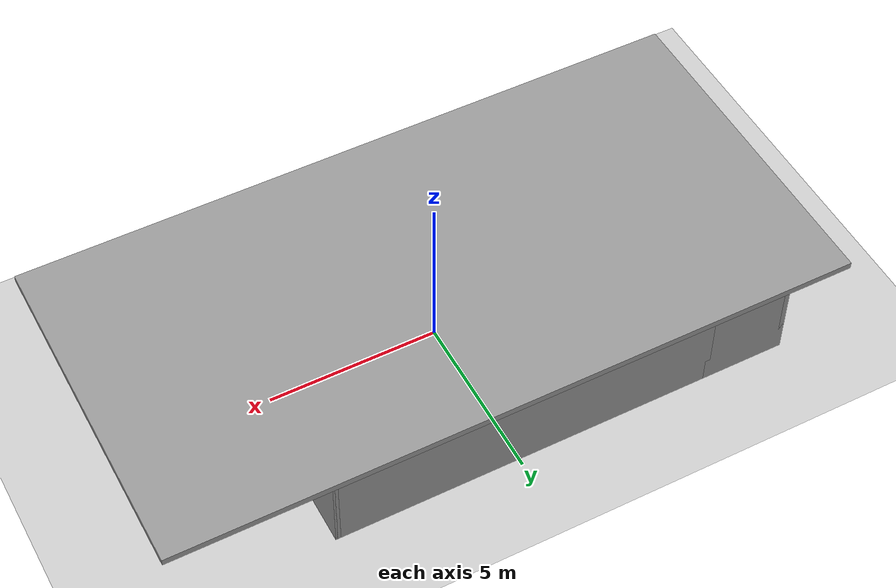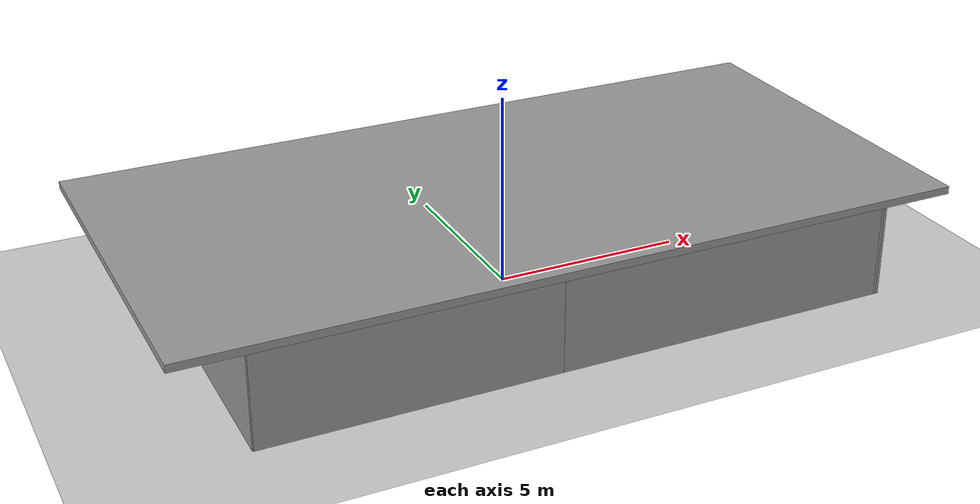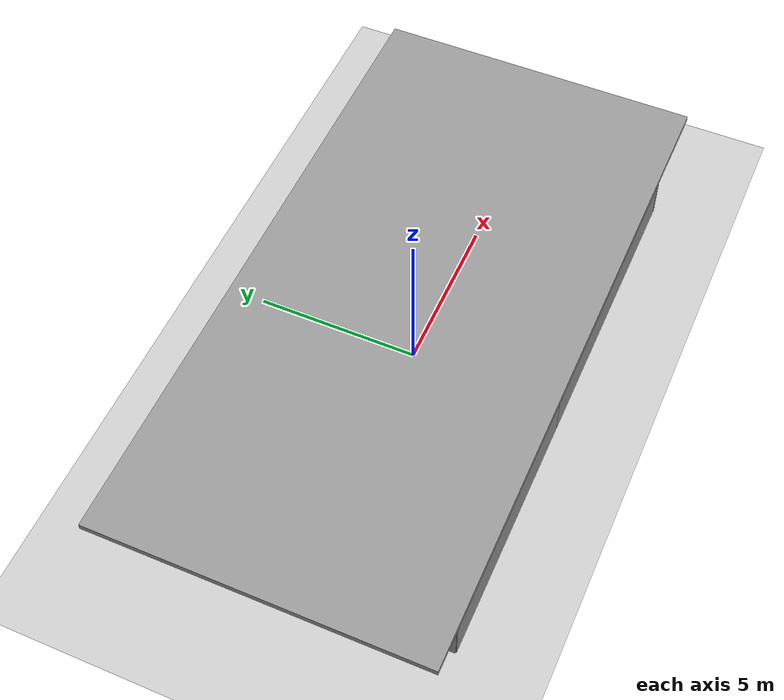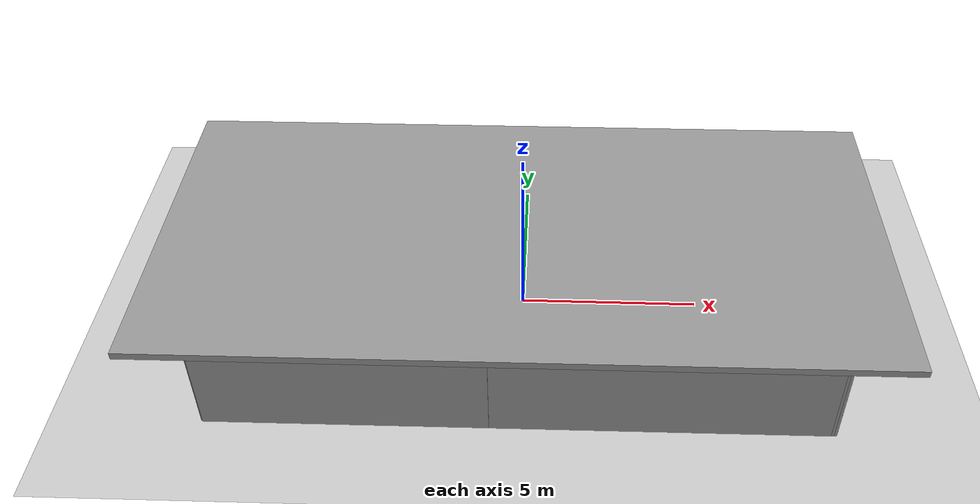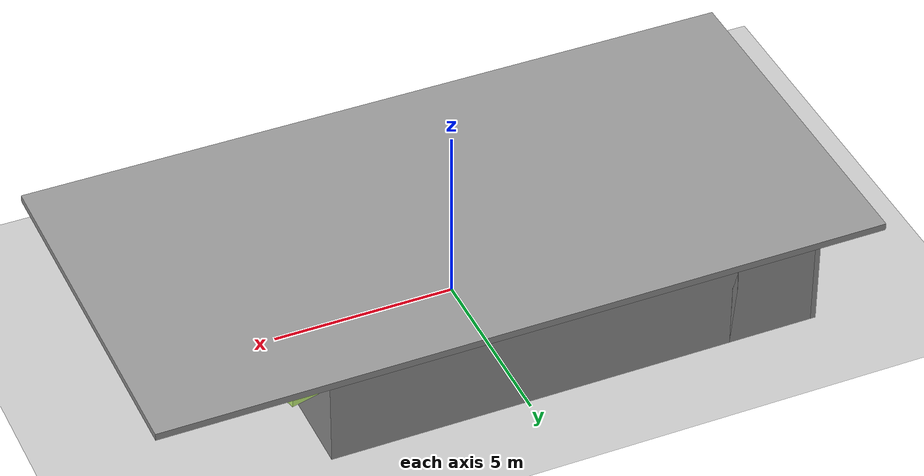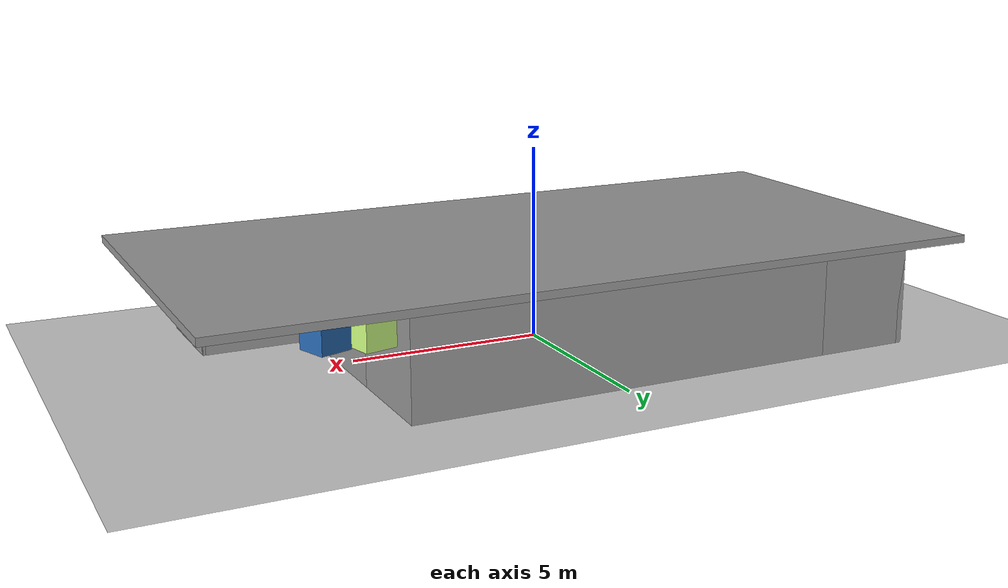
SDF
<sdf version="1.7">
 <world name="default">
  <atmosphere type="adiabatic"/>
  <wind><linear_velocity>0 0 0</linear_velocity></wind>
  <physics name="default_physics" default="1" type="ode">
   <max_step_size>0.001</max_step_size>
   <real_time_factor>1</real_time_factor>
   <real_time_update_rate>1000</real_time_update_rate>
   <max_contacts>20</max_contacts>
   <ode>
    <solver>
     <min_step_size>0.0001</min_step_size>
     <iters>50</iters>
     <sor>1.3</sor>
     <type>quick</type>
     <precon_iters>0</precon_iters>
     <use_dynamic_moi_rescaling>0</use_dynamic_moi_rescaling>
     <friction_model>pyramid_model</friction_model>
    </solver>
    <constraints>
     <cfm>0</cfm>
     <erp>0.2</erp>
     <contact_surface_layer>0.001</contact_surface_layer>
     <contact_max_correcting_vel>100</contact_max_correcting_vel>
    </constraints>
   </ode>
  </physics>
  <gravity>0 0 -9.8</gravity>
  <model name="demo_clean">
   <static>1</static>
   <link name="Wall_0">
    <collision name="Wall_0_Collision">
     <geometry><box><size>5.5 0.15 2.5</size></box></geometry>
     <pose>0 0 1.25 0 -0 0</pose>
     <surface>
      <friction>
       <ode><mu>1</mu><mu2>1</mu2><fdir1>0 0 0</fdir1><slip1>0</slip1><slip2>0</slip2></ode>
       <torsional>
        <coefficient>1</coefficient>
        <patch_radius>0</patch_radius>
        <surface_radius>0</surface_radius>
        <use_patch_radius>1</use_patch_radius>
        <ode><slip>0</slip></ode>
       </torsional>
      </friction>
      <bounce><restitution_coefficient>0</restitution_coefficient><threshold>1e+06</threshold></bounce>
      <contact>
       <collide_without_contact>0</collide_without_contact>
       <collide_without_contact_bitmask>1</collide_without_contact_bitmask>
       <collide_bitmask>1</collide_bitmask>
       <ode>
        <soft_cfm>0</soft_cfm>
        <soft_erp>0.2</soft_erp>
        <kp>1e+13</kp>
        <kd>1</kd>
        <max_vel>0.01</max_vel>
        <min_depth>0</min_depth>
       </ode>
       <bullet>
        <split_impulse>1</split_impulse>
        <split_impulse_penetration_threshold>-0.01</split_impulse_penetration_threshold>
        <soft_cfm>0</soft_cfm>
        <soft_erp>0.2</soft_erp>
        <kp>1e+13</kp>
        <kd>1</kd>
       </bullet>
      </contact>
     </surface>
    </collision>
    <visual name="Wall_0_Visual">
     <geometry><box><size>5.5 0.15 2.5</size></box></geometry>
     <material>
      <script><name>Gazebo/Grey</name><uri>file://media/materials/scripts/gazebo.material</uri></script>
      <ambient>1 1 1 1</ambient>
      <shader type="pixel"><normal_map>default</normal_map></shader>
     </material>
     <pose>0 0 1.25 0 -0 0</pose>
    </visual>
    <pose>-8.14649 2.06618 0 0 0 -1.5708</pose>
   </link>
   <link name="Wall_1">
    <collision name="Wall_1_Collision">
     <geometry><box><size>4.27044 0.15 2.5</size></box></geometry>
     <pose>0 0 1.25 0 -0 0</pose>
     <surface>
      <friction>
       <ode><mu>1</mu><mu2>1</mu2><fdir1>0 0 0</fdir1><slip1>0</slip1><slip2>0</slip2></ode>
       <torsional>
        <coefficient>1</coefficient>
        <patch_radius>0</patch_radius>
        <surface_radius>0</surface_radius>
        <use_patch_radius>1</use_patch_radius>
        <ode><slip>0</slip></ode>
       </torsional>
      </friction>
      <bounce><restitution_coefficient>0</restitution_coefficient><threshold>1e+06</threshold></bounce>
      <contact>
       <collide_without_contact>0</collide_without_contact>
       <collide_without_contact_bitmask>1</collide_without_contact_bitmask>
       <collide_bitmask>1</collide_bitmask>
       <ode>
        <soft_cfm>0</soft_cfm>
        <soft_erp>0.2</soft_erp>
        <kp>1e+13</kp>
        <kd>1</kd>
        <max_vel>0.01</max_vel>
        <min_depth>0</min_depth>
       </ode>
       <bullet>
        <split_impulse>1</split_impulse>
        <split_impulse_penetration_threshold>-0.01</split_impulse_penetration_threshold>
        <soft_cfm>0</soft_cfm>
        <soft_erp>0.2</soft_erp>
        <kp>1e+13</kp>
        <kd>1</kd>
       </bullet>
      </contact>
     </surface>
    </collision>
    <visual name="Wall_1_Visual">
     <geometry><box><size>4.27044 0.15 2.5</size></box></geometry>
     <material>
      <script><name>Gazebo/Grey</name><uri>file://media/materials/scripts/gazebo.material</uri></script>
      <ambient>1 1 1 1</ambient>
      <shader type="pixel"><normal_map>default</normal_map></shader>
     </material>
     <pose>0 0 1.25 0 -0 0</pose>
    </visual>
    <pose>-8.17617 -2.66151 0 0 0 -1.58051</pose>
   </link>
   <link name="Wall_10">
    <collision name="Wall_10_Collision">
     <geometry><box><size>3 0.15 2.5</size></box></geometry>
     <pose>0 0 1.25 0 -0 0</pose>
     <surface>
      <friction>
       <ode><mu>1</mu><mu2>1</mu2><fdir1>0 0 0</fdir1><slip1>0</slip1><slip2>0</slip2></ode>
       <torsional>
        <coefficient>1</coefficient>
        <patch_radius>0</patch_radius>
        <surface_radius>0</surface_radius>
        <use_patch_radius>1</use_patch_radius>
        <ode><slip>0</slip></ode>
       </torsional>
      </friction>
      <bounce><restitution_coefficient>0</restitution_coefficient><threshold>1e+06</threshold></bounce>
      <contact>
       <collide_without_contact>0</collide_without_contact>
       <collide_without_contact_bitmask>1</collide_without_contact_bitmask>
       <collide_bitmask>1</collide_bitmask>
       <ode>
        <soft_cfm>0</soft_cfm>
        <soft_erp>0.2</soft_erp>
        <kp>1e+13</kp>
        <kd>1</kd>
        <max_vel>0.01</max_vel>
        <min_depth>0</min_depth>
       </ode>
       <bullet>
        <split_impulse>1</split_impulse>
        <split_impulse_penetration_threshold>-0.01</split_impulse_penetration_threshold>
        <soft_cfm>0</soft_cfm>
        <soft_erp>0.2</soft_erp>
        <kp>1e+13</kp>
        <kd>1</kd>
       </bullet>
      </contact>
     </surface>
    </collision>
    <visual name="Wall_10_Visual">
     <geometry><box><size>3 0.15 2.5</size></box></geometry>
     <material>
      <script><name>Gazebo/Grey</name><uri>file://media/materials/scripts/gazebo.material</uri></script>
      <ambient>1 1 1 1</ambient>
      <shader type="pixel"><normal_map>default</normal_map></shader>
     </material>
     <pose>0 0 1.25 0 -0 0</pose>
    </visual>
    <pose>5.30351 3.31618 0 0 0 -1.5708</pose>
   </link>
   <link name="Wall_11">
    <collision name="Wall_11_Collision">
     <geometry><box><size>4 0.15 2.5</size></box></geometry>
     <pose>0 0 1.25 0 -0 0</pose>
     <surface>
      <friction>
       <ode><mu>1</mu><mu2>1</mu2><fdir1>0 0 0</fdir1><slip1>0</slip1><slip2>0</slip2></ode>
       <torsional>
        <coefficient>1</coefficient>
        <patch_radius>0</patch_radius>
        <surface_radius>0</surface_radius>
        <use_patch_radius>1</use_patch_radius>
        <ode><slip>0</slip></ode>
       </torsional>
      </friction>
      <bounce><restitution_coefficient>0</restitution_coefficient><threshold>1e+06</threshold></bounce>
      <contact>
       <collide_without_contact>0</collide_without_contact>
       <collide_without_contact_bitmask>1</collide_without_contact_bitmask>
       <collide_bitmask>1</collide_bitmask>
       <ode>
        <soft_cfm>0</soft_cfm>
        <soft_erp>0.2</soft_erp>
        <kp>1e+13</kp>
        <kd>1</kd>
        <max_vel>0.01</max_vel>
        <min_depth>0</min_depth>
       </ode>
       <bullet>
        <split_impulse>1</split_impulse>
        <split_impulse_penetration_threshold>-0.01</split_impulse_penetration_threshold>
        <soft_cfm>0</soft_cfm>
        <soft_erp>0.2</soft_erp>
        <kp>1e+13</kp>
        <kd>1</kd>
       </bullet>
      </contact>
     </surface>
    </collision>
    <visual name="Wall_11_Visual">
     <geometry><box><size>4 0.15 2.5</size></box></geometry>
     <material>
      <script><name>Gazebo/Grey</name><uri>file://media/materials/scripts/gazebo.material</uri></script>
      <ambient>1 1 1 1</ambient>
      <shader type="pixel"><normal_map>default</normal_map></shader>
     </material>
     <pose>0 0 1.25 0 -0 0</pose>
    </visual>
    <pose>3.37851 1.89118 0 0 -0 3.14159</pose>
   </link>
   <link name="Wall_13">
    <collision name="Wall_13_Collision">
     <geometry><box><size>4.25 0.15 2.5</size></box></geometry>
     <pose>0 0 1.25 0 -0 0</pose>
     <surface>
      <friction>
       <ode><mu>1</mu><mu2>1</mu2><fdir1>0 0 0</fdir1><slip1>0</slip1><slip2>0</slip2></ode>
       <torsional>
        <coefficient>1</coefficient>
        <patch_radius>0</patch_radius>
        <surface_radius>0</surface_radius>
        <use_patch_radius>1</use_patch_radius>
        <ode><slip>0</slip></ode>
       </torsional>
      </friction>
      <bounce><restitution_coefficient>0</restitution_coefficient><threshold>1e+06</threshold></bounce>
      <contact>
       <collide_without_contact>0</collide_without_contact>
       <collide_without_contact_bitmask>1</collide_without_contact_bitmask>
       <collide_bitmask>1</collide_bitmask>
       <ode>
        <soft_cfm>0</soft_cfm>
        <soft_erp>0.2</soft_erp>
        <kp>1e+13</kp>
        <kd>1</kd>
        <max_vel>0.01</max_vel>
        <min_depth>0</min_depth>
       </ode>
       <bullet>
        <split_impulse>1</split_impulse>
        <split_impulse_penetration_threshold>-0.01</split_impulse_penetration_threshold>
        <soft_cfm>0</soft_cfm>
        <soft_erp>0.2</soft_erp>
        <kp>1e+13</kp>
        <kd>1</kd>
       </bullet>
      </contact>
     </surface>
    </collision>
    <visual name="Wall_13_Visual">
     <geometry><box><size>4.25 0.15 2.5</size></box></geometry>
     <material>
      <script><name>Gazebo/Grey</name><uri>file://media/materials/scripts/gazebo.material</uri></script>
      <ambient>1 1 1 1</ambient>
      <shader type="pixel"><normal_map>default</normal_map></shader>
     </material>
     <pose>0 0 1.25 0 -0 0</pose>
    </visual>
    <pose>5.30351 -0.158824 0 0 0 -1.5708</pose>
   </link>
   <link name="Wall_14">
    <collision name="Wall_14_Collision">
     <geometry><box><size>3 0.15 2.5</size></box></geometry>
     <pose>0 0 1.25 0 -0 0</pose>
     <surface>
      <friction>
       <ode><mu>1</mu><mu2>1</mu2><fdir1>0 0 0</fdir1><slip1>0</slip1><slip2>0</slip2></ode>
       <torsional>
        <coefficient>1</coefficient>
        <patch_radius>0</patch_radius>
        <surface_radius>0</surface_radius>
        <use_patch_radius>1</use_patch_radius>
        <ode><slip>0</slip></ode>
       </torsional>
      </friction>
      <bounce><restitution_coefficient>0</restitution_coefficient><threshold>1e+06</threshold></bounce>
      <contact>
       <collide_without_contact>0</collide_without_contact>
       <collide_without_contact_bitmask>1</collide_without_contact_bitmask>
       <collide_bitmask>1</collide_bitmask>
       <ode>
        <soft_cfm>0</soft_cfm>
        <soft_erp>0.2</soft_erp>
        <kp>1e+13</kp>
        <kd>1</kd>
        <max_vel>0.01</max_vel>
        <min_depth>0</min_depth>
       </ode>
       <bullet>
        <split_impulse>1</split_impulse>
        <split_impulse_penetration_threshold>-0.01</split_impulse_penetration_threshold>
        <soft_cfm>0</soft_cfm>
        <soft_erp>0.2</soft_erp>
        <kp>1e+13</kp>
        <kd>1</kd>
       </bullet>
      </contact>
     </surface>
    </collision>
    <visual name="Wall_14_Visual">
     <geometry><box><size>3 0.15 2.5</size></box></geometry>
     <material>
      <script><name>Gazebo/Grey</name><uri>file://media/materials/scripts/gazebo.material</uri></script>
      <ambient>1 1 1 1</ambient>
      <shader type="pixel"><normal_map>default</normal_map></shader>
     </material>
     <pose>0 0 1.25 0 -0 0</pose>
    </visual>
    <pose>6.72851 -2.20882 0 0 -0 0</pose>
   </link>
   <link name="Wall_15">
    <collision name="Wall_15_Collision">
     <geometry><box><size>2.6816 0.15 2.5</size></box></geometry>
     <pose>0 0 1.25 0 -0 0</pose>
     <surface>
      <friction>
       <ode><mu>1</mu><mu2>1</mu2><fdir1>0 0 0</fdir1><slip1>0</slip1><slip2>0</slip2></ode>
       <torsional>
        <coefficient>1</coefficient>
        <patch_radius>0</patch_radius>
        <surface_radius>0</surface_radius>
        <use_patch_radius>1</use_patch_radius>
        <ode><slip>0</slip></ode>
       </torsional>
      </friction>
      <bounce><restitution_coefficient>0</restitution_coefficient><threshold>1e+06</threshold></bounce>
      <contact>
       <collide_without_contact>0</collide_without_contact>
       <collide_without_contact_bitmask>1</collide_without_contact_bitmask>
       <collide_bitmask>1</collide_bitmask>
       <ode>
        <soft_cfm>0</soft_cfm>
        <soft_erp>0.2</soft_erp>
        <kp>1e+13</kp>
        <kd>1</kd>
        <max_vel>0.01</max_vel>
        <min_depth>0</min_depth>
       </ode>
       <bullet>
        <split_impulse>1</split_impulse>
        <split_impulse_penetration_threshold>-0.01</split_impulse_penetration_threshold>
        <soft_cfm>0</soft_cfm>
        <soft_erp>0.2</soft_erp>
        <kp>1e+13</kp>
        <kd>1</kd>
       </bullet>
      </contact>
     </surface>
    </collision>
    <visual name="Wall_15_Visual">
     <geometry><box><size>2.6816 0.15 2.5</size></box></geometry>
     <material>
      <script><name>Gazebo/Grey</name><uri>file://media/materials/scripts/gazebo.material</uri></script>
      <ambient>1 1 1 1</ambient>
      <shader type="pixel"><normal_map>default</normal_map></shader>
     </material>
     <pose>0 0 1.25 0 -0 0</pose>
    </visual>
    <pose>8.16988 -3.47452 0 0 0 -1.55787</pose>
   </link>
   <link name="Wall_16">
    <collision name="Wall_16_Collision">
     <geometry><box><size>9 0.15 2.5</size></box></geometry>
     <pose>0 0 1.25 0 -0 0</pose>
     <surface>
      <friction>
       <ode><mu>1</mu><mu2>1</mu2><fdir1>0 0 0</fdir1><slip1>0</slip1><slip2>0</slip2></ode>
       <torsional>
        <coefficient>1</coefficient>
        <patch_radius>0</patch_radius>
        <surface_radius>0</surface_radius>
        <use_patch_radius>1</use_patch_radius>
        <ode><slip>0</slip></ode>
       </torsional>
      </friction>
      <bounce><restitution_coefficient>0</restitution_coefficient><threshold>1e+06</threshold></bounce>
      <contact>
       <collide_without_contact>0</collide_without_contact>
       <collide_without_contact_bitmask>1</collide_without_contact_bitmask>
       <collide_bitmask>1</collide_bitmask>
       <ode>
        <soft_cfm>0</soft_cfm>
        <soft_erp>0.2</soft_erp>
        <kp>1e+13</kp>
        <kd>1</kd>
        <max_vel>0.01</max_vel>
        <min_depth>0</min_depth>
       </ode>
       <bullet>
        <split_impulse>1</split_impulse>
        <split_impulse_penetration_threshold>-0.01</split_impulse_penetration_threshold>
        <soft_cfm>0</soft_cfm>
        <soft_erp>0.2</soft_erp>
        <kp>1e+13</kp>
        <kd>1</kd>
       </bullet>
      </contact>
     </surface>
    </collision>
    <visual name="Wall_16_Visual">
     <geometry><box><size>9 0.15 2.5</size></box></geometry>
     <material>
      <script><name>Gazebo/Grey</name><uri>file://media/materials/scripts/gazebo.material</uri></script>
      <ambient>1 1 1 1</ambient>
      <shader type="pixel"><normal_map>default</normal_map></shader>
     </material>
     <pose>0 0 1.25 0 -0 0</pose>
    </visual>
    <pose>3.76125 -4.74021 0 0 -0 3.14159</pose>
   </link>
   <link name="Wall_19">
    <collision name="Wall_19_Collision">
     <geometry><box><size>2.34163 0.15 2.5</size></box></geometry>
     <pose>0 0 1.25 0 -0 0</pose>
     <surface>
      <friction>
       <ode><mu>1</mu><mu2>1</mu2><fdir1>0 0 0</fdir1><slip1>0</slip1><slip2>0</slip2></ode>
       <torsional>
        <coefficient>1</coefficient>
        <patch_radius>0</patch_radius>
        <surface_radius>0</surface_radius>
        <use_patch_radius>1</use_patch_radius>
        <ode><slip>0</slip></ode>
       </torsional>
      </friction>
      <bounce><restitution_coefficient>0</restitution_coefficient><threshold>1e+06</threshold></bounce>
      <contact>
       <collide_without_contact>0</collide_without_contact>
       <collide_without_contact_bitmask>1</collide_without_contact_bitmask>
       <collide_bitmask>1</collide_bitmask>
       <ode>
        <soft_cfm>0</soft_cfm>
        <soft_erp>0.2</soft_erp>
        <kp>1e+13</kp>
        <kd>1</kd>
        <max_vel>0.01</max_vel>
        <min_depth>0</min_depth>
       </ode>
       <bullet>
        <split_impulse>1</split_impulse>
        <split_impulse_penetration_threshold>-0.01</split_impulse_penetration_threshold>
        <soft_cfm>0</soft_cfm>
        <soft_erp>0.2</soft_erp>
        <kp>1e+13</kp>
        <kd>1</kd>
       </bullet>
      </contact>
     </surface>
    </collision>
    <visual name="Wall_19_Visual">
     <geometry><box><size>2.34163 0.15 2.5</size></box></geometry>
     <material>
      <script><name>Gazebo/Grey</name><uri>file://media/materials/scripts/gazebo.material</uri></script>
      <ambient>1 1 1 1</ambient>
      <shader type="pixel"><normal_map>default</normal_map></shader>
     </material>
     <pose>0 0 1.25 0 -0 0</pose>
    </visual>
    <inertial>
     <inertia><ixx>0</ixx><iyy>0</iyy><izz>0</izz><ixy>0</ixy><ixz>0</ixz><iyz>0</iyz></inertia>
     <mass>1</mass>
    </inertial>
    <pose>0.295923 -2.24288 0 0 -0 0</pose>
   </link>
   <link name="Wall_2">
    <collision name="Wall_2_Collision">
     <geometry><box><size>7.5 0.15 2.5</size></box></geometry>
     <pose>0 0 1.25 0 -0 0</pose>
     <surface>
      <friction>
       <ode><mu>1</mu><mu2>1</mu2><fdir1>0 0 0</fdir1><slip1>0</slip1><slip2>0</slip2></ode>
       <torsional>
        <coefficient>1</coefficient>
        <patch_radius>0</patch_radius>
        <surface_radius>0</surface_radius>
        <use_patch_radius>1</use_patch_radius>
        <ode><slip>0</slip></ode>
       </torsional>
      </friction>
      <bounce><restitution_coefficient>0</restitution_coefficient><threshold>1e+06</threshold></bounce>
      <contact>
       <collide_without_contact>0</collide_without_contact>
       <collide_without_contact_bitmask>1</collide_without_contact_bitmask>
       <collide_bitmask>1</collide_bitmask>
       <ode>
        <soft_cfm>0</soft_cfm>
        <soft_erp>0.2</soft_erp>
        <kp>1e+13</kp>
        <kd>1</kd>
        <max_vel>0.01</max_vel>
        <min_depth>0</min_depth>
       </ode>
       <bullet>
        <split_impulse>1</split_impulse>
        <split_impulse_penetration_threshold>-0.01</split_impulse_penetration_threshold>
        <soft_cfm>0</soft_cfm>
        <soft_erp>0.2</soft_erp>
        <kp>1e+13</kp>
        <kd>1</kd>
       </bullet>
      </contact>
     </surface>
    </collision>
    <visual name="Wall_2_Visual">
     <geometry><box><size>7.5 0.15 2.5</size></box></geometry>
     <material>
      <script><name>Gazebo/Grey</name><uri>file://media/materials/scripts/gazebo.material</uri></script>
      <ambient>1 1 1 1</ambient>
      <shader type="pixel"><normal_map>default</normal_map></shader>
     </material>
     <pose>0 0 1.25 0 -0 0</pose>
    </visual>
    <pose>-4.49149 -4.74 0 0 -0 0</pose>
   </link>
   <link name="Wall_21">
    <collision name="Wall_21_Collision">
     <geometry><box><size>2.5 0.15 2.5</size></box></geometry>
     <pose>0 0 1.25 0 -0 0</pose>
     <surface>
      <friction>
       <ode><mu>1</mu><mu2>1</mu2><fdir1>0 0 0</fdir1><slip1>0</slip1><slip2>0</slip2></ode>
       <torsional>
        <coefficient>1</coefficient>
        <patch_radius>0</patch_radius>
        <surface_radius>0</surface_radius>
        <use_patch_radius>1</use_patch_radius>
        <ode><slip>0</slip></ode>
       </torsional>
      </friction>
      <bounce><restitution_coefficient>0</restitution_coefficient><threshold>1e+06</threshold></bounce>
      <contact>
       <collide_without_contact>0</collide_without_contact>
       <collide_without_contact_bitmask>1</collide_without_contact_bitmask>
       <collide_bitmask>1</collide_bitmask>
       <ode>
        <soft_cfm>0</soft_cfm>
        <soft_erp>0.2</soft_erp>
        <kp>1e+13</kp>
        <kd>1</kd>
        <max_vel>0.01</max_vel>
        <min_depth>0</min_depth>
       </ode>
       <bullet>
        <split_impulse>1</split_impulse>
        <split_impulse_penetration_threshold>-0.01</split_impulse_penetration_threshold>
        <soft_cfm>0</soft_cfm>
        <soft_erp>0.2</soft_erp>
        <kp>1e+13</kp>
        <kd>1</kd>
       </bullet>
      </contact>
     </surface>
    </collision>
    <visual name="Wall_21_Visual">
     <geometry><box><size>2.5 0.15 2.5</size></box></geometry>
     <material>
      <script><name>Gazebo/Grey</name><uri>file://media/materials/scripts/gazebo.material</uri></script>
      <ambient>1 1 1 1</ambient>
      <shader type="pixel"><normal_map>default</normal_map></shader>
     </material>
     <pose>0 0 1.25 0 -0 0</pose>
    </visual>
    <pose>0.573753 -3.46553 0 0 0 -1.5708</pose>
   </link>
   <link name="Wall_21_clone">
    <collision name="Wall_21_Collision">
     <geometry><box><size>0.240964 0.15 2.5</size></box></geometry>
     <pose>0 0 1.25 0 -0 0</pose>
     <surface>
      <friction>
       <ode><mu>1</mu><mu2>1</mu2><fdir1>0 0 0</fdir1><slip1>0</slip1><slip2>0</slip2></ode>
       <torsional>
        <coefficient>1</coefficient>
        <patch_radius>0</patch_radius>
        <surface_radius>0</surface_radius>
        <use_patch_radius>1</use_patch_radius>
        <ode><slip>0</slip></ode>
       </torsional>
      </friction>
      <bounce><restitution_coefficient>0</restitution_coefficient><threshold>1e+06</threshold></bounce>
      <contact>
       <collide_without_contact>0</collide_without_contact>
       <collide_without_contact_bitmask>1</collide_without_contact_bitmask>
       <collide_bitmask>1</collide_bitmask>
       <ode>
        <soft_cfm>0</soft_cfm>
        <soft_erp>0.2</soft_erp>
        <kp>1e+13</kp>
        <kd>1</kd>
        <max_vel>0.01</max_vel>
        <min_depth>0</min_depth>
       </ode>
       <bullet>
        <split_impulse>1</split_impulse>
        <split_impulse_penetration_threshold>-0.01</split_impulse_penetration_threshold>
        <soft_cfm>0</soft_cfm>
        <soft_erp>0.2</soft_erp>
        <kp>1e+13</kp>
        <kd>1</kd>
       </bullet>
      </contact>
     </surface>
    </collision>
    <visual name="Wall_21_Visual">
     <geometry><box><size>0.240964 0.15 2.5</size></box></geometry>
     <material>
      <script><name>Gazebo/Grey</name><uri>file://media/materials/scripts/gazebo.material</uri></script>
      <ambient>1 1 1 1</ambient>
      <shader type="pixel"><normal_map>default</normal_map></shader>
     </material>
     <pose>0 0 1.25 0 -0 0</pose>
    </visual>
    <inertial>
     <inertia><ixx>0</ixx><iyy>0</iyy><izz>0</izz><ixy>0</ixy><ixz>0</ixz><iyz>0</iyz></inertia>
     <mass>1</mass>
    </inertial>
    <pose>-0.802658 -0.717313 0 0 0 -1.5708</pose>
   </link>
   <link name="Wall_21_clone_0">
    <collision name="Wall_21_Collision">
     <geometry><box><size>0.394105 0.15 2.5</size></box></geometry>
     <pose>0 0 1.25 0 -0 0</pose>
     <surface>
      <friction>
       <ode><mu>1</mu><mu2>1</mu2><fdir1>0 0 0</fdir1><slip1>0</slip1><slip2>0</slip2></ode>
       <torsional>
        <coefficient>1</coefficient>
        <patch_radius>0</patch_radius>
        <surface_radius>0</surface_radius>
        <use_patch_radius>1</use_patch_radius>
        <ode><slip>0</slip></ode>
       </torsional>
      </friction>
      <bounce><restitution_coefficient>0</restitution_coefficient><threshold>1e+06</threshold></bounce>
      <contact>
       <collide_without_contact>0</collide_without_contact>
       <collide_without_contact_bitmask>1</collide_without_contact_bitmask>
       <collide_bitmask>1</collide_bitmask>
       <ode>
        <soft_cfm>0</soft_cfm>
        <soft_erp>0.2</soft_erp>
        <kp>1e+13</kp>
        <kd>1</kd>
        <max_vel>0.01</max_vel>
        <min_depth>0</min_depth>
       </ode>
       <bullet>
        <split_impulse>1</split_impulse>
        <split_impulse_penetration_threshold>-0.01</split_impulse_penetration_threshold>
        <soft_cfm>0</soft_cfm>
        <soft_erp>0.2</soft_erp>
        <kp>1e+13</kp>
        <kd>1</kd>
       </bullet>
      </contact>
     </surface>
    </collision>
    <visual name="Wall_21_Visual">
     <geometry><box><size>0.394105 0.15 2.5</size></box></geometry>
     <material>
      <script><name>Gazebo/Grey</name><uri>file://media/materials/scripts/gazebo.material</uri></script>
      <ambient>1 1 1 1</ambient>
      <shader type="pixel"><normal_map>default</normal_map></shader>
     </material>
     <pose>0 0 1.25 0 -0 0</pose>
    </visual>
    <inertial>
     <inertia><ixx>0</ixx><iyy>0</iyy><izz>0</izz><ixy>0</ixy><ixz>0</ixz><iyz>0</iyz></inertia>
     <mass>1</mass>
    </inertial>
    <pose>-0.820336 -2.26773 0 0 0 -1.5708</pose>
   </link>
   <link name="Wall_21_clone_0_clone_0_clone_clone">
    <gravity>0</gravity>
    <collision name="Wall_21_Collision">
     <geometry><box><size>1.1941 0.15 1.96033</size></box></geometry>
     <pose>0 0 1.25 0 -0 0</pose>
     <surface>
      <friction>
       <ode><mu>1</mu><mu2>1</mu2><fdir1>0 0 0</fdir1><slip1>0</slip1><slip2>0</slip2></ode>
       <torsional>
        <coefficient>1</coefficient>
        <patch_radius>0</patch_radius>
        <surface_radius>0</surface_radius>
        <use_patch_radius>1</use_patch_radius>
        <ode><slip>0</slip></ode>
       </torsional>
      </friction>
      <bounce><restitution_coefficient>0</restitution_coefficient><threshold>1e+06</threshold></bounce>
      <contact>
       <collide_without_contact>0</collide_without_contact>
       <collide_without_contact_bitmask>1</collide_without_contact_bitmask>
       <collide_bitmask>1</collide_bitmask>
       <ode>
        <soft_cfm>0</soft_cfm>
        <soft_erp>0.2</soft_erp>
        <kp>1e+13</kp>
        <kd>1</kd>
        <max_vel>0.01</max_vel>
        <min_depth>0</min_depth>
       </ode>
       <bullet>
        <split_impulse>1</split_impulse>
        <split_impulse_penetration_threshold>-0.01</split_impulse_penetration_threshold>
        <soft_cfm>0</soft_cfm>
        <soft_erp>0.2</soft_erp>
        <kp>1e+13</kp>
        <kd>1</kd>
       </bullet>
      </contact>
     </surface>
    </collision>
    <visual name="Wall_21_Visual">
     <geometry><box><size>1.1941 0.15 1.96033</size></box></geometry>
     <material>
      <script><name>Gazebo/Grey</name><uri>file://media/materials/scripts/gazebo.material</uri></script>
      <ambient>1 1 1 1</ambient>
      <shader type="pixel"><normal_map>__default__</normal_map></shader>
      <diffuse>0.7 0.7 0.7 1</diffuse>
      <specular>0.01 0.01 0.01 1</specular>
      <emissive>0 0 0 1</emissive>
     </material>
     <pose>0 0 1.25 0 -0 0</pose>
    </visual>
    <inertial>
     <inertia><ixx>0</ixx><iyy>0</iyy><izz>0</izz><ixy>0</ixy><ixz>0</ixz><iyz>0</iyz></inertia>
     <mass>1</mass>
    </inertial>
    <pose>-1.47342 -0.839052 -0.23202 0 -0 3.0297</pose>
   </link>
   <link name="Wall_21_clone_0_clone_0_clone_clone_clone_clone">
    <gravity>0</gravity>
    <collision name="Wall_21_Collision">
     <geometry><box><size>0.924919 0.15 1.96033</size></box></geometry>
     <pose>0 0 1.25 0 -0 0</pose>
     <surface>
      <friction>
       <ode><mu>1</mu><mu2>1</mu2><fdir1>0 0 0</fdir1><slip1>0</slip1><slip2>0</slip2></ode>
       <torsional>
        <coefficient>1</coefficient>
        <patch_radius>0</patch_radius>
        <surface_radius>0</surface_radius>
        <use_patch_radius>1</use_patch_radius>
        <ode><slip>0</slip></ode>
       </torsional>
      </friction>
      <bounce><restitution_coefficient>0</restitution_coefficient><threshold>1e+06</threshold></bounce>
      <contact>
       <collide_without_contact>0</collide_without_contact>
       <collide_without_contact_bitmask>1</collide_without_contact_bitmask>
       <collide_bitmask>1</collide_bitmask>
       <ode>
        <soft_cfm>0</soft_cfm>
        <soft_erp>0.2</soft_erp>
        <kp>1e+13</kp>
        <kd>1</kd>
        <max_vel>0.01</max_vel>
        <min_depth>0</min_depth>
       </ode>
       <bullet>
        <split_impulse>1</split_impulse>
        <split_impulse_penetration_threshold>-0.01</split_impulse_penetration_threshold>
        <soft_cfm>0</soft_cfm>
        <soft_erp>0.2</soft_erp>
        <kp>1e+13</kp>
        <kd>1</kd>
       </bullet>
      </contact>
     </surface>
    </collision>
    <visual name="Wall_21_Visual">
     <geometry><box><size>0.924919 0.15 1.96033</size></box></geometry>
     <material>
      <script><name>Gazebo/Grey</name><uri>file://media/materials/scripts/gazebo.material</uri></script>
      <ambient>1 1 1 1</ambient>
      <shader type="pixel"><normal_map>__default__</normal_map></shader>
      <diffuse>0.7 0.7 0.7 1</diffuse>
      <specular>0.01 0.01 0.01 1</specular>
      <emissive>0 0 0 1</emissive>
     </material>
     <pose>0 0 1.25 0 -0 0</pose>
    </visual>
    <inertial>
     <inertia><ixx>0</ixx><iyy>0</iyy><izz>0</izz><ixy>0</ixy><ixz>0</ixz><iyz>0</iyz></inertia>
     <mass>1</mass>
    </inertial>
    <pose>2.0073 -0.280742 -0.23202 0 -0 2.28452</pose>
   </link>
   <link name="Wall_21_clone_0_clone_0_clone_clone_clone_clone_clone_clone_clone_clone">
    <gravity>0</gravity>
    <collision name="Wall_21_Collision">
     <geometry><box><size>0.663949 0.15 1.96033</size></box></geometry>
     <pose>0 0 1.25 0 -0 0</pose>
     <surface>
      <friction>
       <ode><mu>1</mu><mu2>1</mu2><fdir1>0 0 0</fdir1><slip1>0</slip1><slip2>0</slip2></ode>
       <torsional>
        <coefficient>1</coefficient>
        <patch_radius>0</patch_radius>
        <surface_radius>0</surface_radius>
        <use_patch_radius>1</use_patch_radius>
        <ode><slip>0</slip></ode>
       </torsional>
      </friction>
      <bounce><restitution_coefficient>0</restitution_coefficient><threshold>1e+06</threshold></bounce>
      <contact>
       <collide_without_contact>0</collide_without_contact>
       <collide_without_contact_bitmask>1</collide_without_contact_bitmask>
       <collide_bitmask>1</collide_bitmask>
       <ode>
        <soft_cfm>0</soft_cfm>
        <soft_erp>0.2</soft_erp>
        <kp>1e+13</kp>
        <kd>1</kd>
        <max_vel>0.01</max_vel>
        <min_depth>0</min_depth>
       </ode>
       <bullet>
        <split_impulse>1</split_impulse>
        <split_impulse_penetration_threshold>-0.01</split_impulse_penetration_threshold>
        <soft_cfm>0</soft_cfm>
        <soft_erp>0.2</soft_erp>
        <kp>1e+13</kp>
        <kd>1</kd>
       </bullet>
      </contact>
     </surface>
    </collision>
    <visual name="Wall_21_Visual">
     <geometry><box><size>0.663949 0.15 1.96033</size></box></geometry>
     <material>
      <script><name>Gazebo/Grey</name><uri>file://media/materials/scripts/gazebo.material</uri></script>
      <ambient>1 1 1 1</ambient>
      <shader type="pixel"><normal_map>__default__</normal_map></shader>
      <diffuse>0.7 0.7 0.7 1</diffuse>
      <specular>0.01 0.01 0.01 1</specular>
      <emissive>0 0 0 1</emissive>
     </material>
     <pose>0 0 1.25 0 -0 0</pose>
    </visual>
    <inertial>
     <inertia><ixx>0</ixx><iyy>0</iyy><izz>0</izz><ixy>0</ixy><ixz>0</ixz><iyz>0</iyz></inertia>
     <mass>1</mass>
    </inertial>
    <pose>3.68306 -1.18793 -0.23202 0 -0 2.79384</pose>
   </link>
   <link name="Wall_21_clone_0_clone_0_clone_clone_clone_clone_clone_clone_clone_clone_clone_clone">
    <gravity>0</gravity>
    <collision name="Wall_21_Collision">
     <geometry><box><size>0.663949 0.15 1.96033</size></box></geometry>
     <pose>0 0 1.25 0 -0 0</pose>
     <surface>
      <friction>
       <ode><mu>1</mu><mu2>1</mu2><fdir1>0 0 0</fdir1><slip1>0</slip1><slip2>0</slip2></ode>
       <torsional>
        <coefficient>1</coefficient>
        <patch_radius>0</patch_radius>
        <surface_radius>0</surface_radius>
        <use_patch_radius>1</use_patch_radius>
        <ode><slip>0</slip></ode>
       </torsional>
      </friction>
      <bounce><restitution_coefficient>0</restitution_coefficient><threshold>1e+06</threshold></bounce>
      <contact>
       <collide_without_contact>0</collide_without_contact>
       <collide_without_contact_bitmask>1</collide_without_contact_bitmask>
       <collide_bitmask>1</collide_bitmask>
       <ode>
        <soft_cfm>0</soft_cfm>
        <soft_erp>0.2</soft_erp>
        <kp>1e+13</kp>
        <kd>1</kd>
        <max_vel>0.01</max_vel>
        <min_depth>0</min_depth>
       </ode>
       <bullet>
        <split_impulse>1</split_impulse>
        <split_impulse_penetration_threshold>-0.01</split_impulse_penetration_threshold>
        <soft_cfm>0</soft_cfm>
        <soft_erp>0.2</soft_erp>
        <kp>1e+13</kp>
        <kd>1</kd>
       </bullet>
      </contact>
     </surface>
    </collision>
    <visual name="Wall_21_Visual">
     <geometry><box><size>0.663949 0.15 1.96033</size></box></geometry>
     <material>
      <script><name>Gazebo/Grey</name><uri>file://media/materials/scripts/gazebo.material</uri></script>
      <ambient>1 1 1 1</ambient>
      <shader type="pixel"><normal_map>__default__</normal_map></shader>
      <diffuse>0.7 0.7 0.7 1</diffuse>
      <specular>0.01 0.01 0.01 1</specular>
      <emissive>0 0 0 1</emissive>
     </material>
     <pose>0 0 1.25 0 -0 0</pose>
    </visual>
    <inertial>
     <inertia><ixx>0</ixx><iyy>0</iyy><izz>0</izz><ixy>0</ixy><ixz>0</ixz><iyz>0</iyz></inertia>
     <mass>1</mass>
    </inertial>
    <pose>3.65792 -0.364043 -0.23202 0 0 -2.77941</pose>
   </link>
   <link name="Wall_21_clone_clone">
    <collision name="Wall_21_Collision">
     <geometry><box><size>0.240964 0.15 2.5</size></box></geometry>
     <pose>0 0 1.25 0 -0 0</pose>
     <surface>
      <friction>
       <ode><mu>1</mu><mu2>1</mu2><fdir1>0 0 0</fdir1><slip1>0</slip1><slip2>0</slip2></ode>
       <torsional>
        <coefficient>1</coefficient>
        <patch_radius>0</patch_radius>
        <surface_radius>0</surface_radius>
        <use_patch_radius>1</use_patch_radius>
        <ode><slip>0</slip></ode>
       </torsional>
      </friction>
      <bounce><restitution_coefficient>0</restitution_coefficient><threshold>1e+06</threshold></bounce>
      <contact>
       <collide_without_contact>0</collide_without_contact>
       <collide_without_contact_bitmask>1</collide_without_contact_bitmask>
       <collide_bitmask>1</collide_bitmask>
       <ode>
        <soft_cfm>0</soft_cfm>
        <soft_erp>0.2</soft_erp>
        <kp>1e+13</kp>
        <kd>1</kd>
        <max_vel>0.01</max_vel>
        <min_depth>0</min_depth>
       </ode>
       <bullet>
        <split_impulse>1</split_impulse>
        <split_impulse_penetration_threshold>-0.01</split_impulse_penetration_threshold>
        <soft_cfm>0</soft_cfm>
        <soft_erp>0.2</soft_erp>
        <kp>1e+13</kp>
        <kd>1</kd>
       </bullet>
      </contact>
     </surface>
    </collision>
    <visual name="Wall_21_Visual">
     <geometry><box><size>0.240964 0.15 2.5</size></box></geometry>
     <material>
      <script><name>Gazebo/Grey</name><uri>file://media/materials/scripts/gazebo.material</uri></script>
      <ambient>1 1 1 1</ambient>
      <shader type="pixel"><normal_map>default</normal_map></shader>
     </material>
     <pose>0 0 1.25 0 -0 0</pose>
    </visual>
    <inertial>
     <inertia><ixx>0</ixx><iyy>0</iyy><izz>0</izz><ixy>0</ixy><ixz>0</ixz><iyz>0</iyz></inertia>
     <mass>1</mass>
    </inertial>
    <pose>-0.824993 -4.62184 0 0 0 -1.5708</pose>
   </link>
   <link name="Wall_23">
    <collision name="Wall_23_Collision">
     <geometry><box><size>0.981708 0.15 2.5</size></box></geometry>
     <pose>0 0 1.25 0 -0 0</pose>
     <surface>
      <friction>
       <ode><mu>1</mu><mu2>1</mu2><fdir1>0 0 0</fdir1><slip1>0</slip1><slip2>0</slip2></ode>
       <torsional>
        <coefficient>1</coefficient>
        <patch_radius>0</patch_radius>
        <surface_radius>0</surface_radius>
        <use_patch_radius>1</use_patch_radius>
        <ode><slip>0</slip></ode>
       </torsional>
      </friction>
      <bounce><restitution_coefficient>0</restitution_coefficient><threshold>1e+06</threshold></bounce>
      <contact>
       <collide_without_contact>0</collide_without_contact>
       <collide_without_contact_bitmask>1</collide_without_contact_bitmask>
       <collide_bitmask>1</collide_bitmask>
       <ode>
        <soft_cfm>0</soft_cfm>
        <soft_erp>0.2</soft_erp>
        <kp>1e+13</kp>
        <kd>1</kd>
        <max_vel>0.01</max_vel>
        <min_depth>0</min_depth>
       </ode>
       <bullet>
        <split_impulse>1</split_impulse>
        <split_impulse_penetration_threshold>-0.01</split_impulse_penetration_threshold>
        <soft_cfm>0</soft_cfm>
        <soft_erp>0.2</soft_erp>
        <kp>1e+13</kp>
        <kd>1</kd>
       </bullet>
      </contact>
     </surface>
    </collision>
    <visual name="Wall_23_Visual">
     <geometry><box><size>0.981708 0.15 2.5</size></box></geometry>
     <material>
      <script><name>Gazebo/Grey</name><uri>file://media/materials/scripts/gazebo.material</uri></script>
      <ambient>1 1 1 1</ambient>
      <shader type="pixel"><normal_map>default</normal_map></shader>
     </material>
     <pose>0 0 1.25 0 -0 0</pose>
    </visual>
    <inertial>
     <inertia><ixx>0</ixx><iyy>0</iyy><izz>0</izz><ixy>0</ixy><ixz>0</ixz><iyz>0</iyz></inertia>
     <mass>1</mass>
    </inertial>
    <pose>0.983425 -3.07697 0 0 -0 0</pose>
   </link>
   <link name="Wall_25">
    <collision name="Wall_25_Collision">
     <geometry><box><size>1 0.15 2.5</size></box></geometry>
     <pose>0 0 1.25 0 -0 0</pose>
     <surface>
      <friction>
       <ode><mu>1</mu><mu2>1</mu2><fdir1>0 0 0</fdir1><slip1>0</slip1><slip2>0</slip2></ode>
       <torsional>
        <coefficient>1</coefficient>
        <patch_radius>0</patch_radius>
        <surface_radius>0</surface_radius>
        <use_patch_radius>1</use_patch_radius>
        <ode><slip>0</slip></ode>
       </torsional>
      </friction>
      <bounce><restitution_coefficient>0</restitution_coefficient><threshold>1e+06</threshold></bounce>
      <contact>
       <collide_without_contact>0</collide_without_contact>
       <collide_without_contact_bitmask>1</collide_without_contact_bitmask>
       <collide_bitmask>1</collide_bitmask>
       <ode>
        <soft_cfm>0</soft_cfm>
        <soft_erp>0.2</soft_erp>
        <kp>1e+13</kp>
        <kd>1</kd>
        <max_vel>0.01</max_vel>
        <min_depth>0</min_depth>
       </ode>
       <bullet>
        <split_impulse>1</split_impulse>
        <split_impulse_penetration_threshold>-0.01</split_impulse_penetration_threshold>
        <soft_cfm>0</soft_cfm>
        <soft_erp>0.2</soft_erp>
        <kp>1e+13</kp>
        <kd>1</kd>
       </bullet>
      </contact>
     </surface>
    </collision>
    <visual name="Wall_25_Visual">
     <geometry><box><size>1 0.15 2.5</size></box></geometry>
     <material>
      <script><name>Gazebo/Grey</name><uri>file://media/materials/scripts/gazebo.material</uri></script>
      <ambient>1 1 1 1</ambient>
      <shader type="pixel"><normal_map>default</normal_map></shader>
     </material>
     <pose>0 0 1.25 0 -0 0</pose>
    </visual>
    <pose>1.30015 4.30512 0 0 0 -1.5708</pose>
   </link>
   <link name="Wall_27">
    <collision name="Wall_27_Collision">
     <geometry><box><size>3.5 0.15 2.5</size></box></geometry>
     <pose>0 0 1.25 0 -0 0</pose>
     <surface>
      <friction>
       <ode><mu>1</mu><mu2>1</mu2><fdir1>0 0 0</fdir1><slip1>0</slip1><slip2>0</slip2></ode>
       <torsional>
        <coefficient>1</coefficient>
        <patch_radius>0</patch_radius>
        <surface_radius>0</surface_radius>
        <use_patch_radius>1</use_patch_radius>
        <ode><slip>0</slip></ode>
       </torsional>
      </friction>
      <bounce><restitution_coefficient>0</restitution_coefficient><threshold>1e+06</threshold></bounce>
      <contact>
       <collide_without_contact>0</collide_without_contact>
       <collide_without_contact_bitmask>1</collide_without_contact_bitmask>
       <collide_bitmask>1</collide_bitmask>
       <ode>
        <soft_cfm>0</soft_cfm>
        <soft_erp>0.2</soft_erp>
        <kp>1e+13</kp>
        <kd>1</kd>
        <max_vel>0.01</max_vel>
        <min_depth>0</min_depth>
       </ode>
       <bullet>
        <split_impulse>1</split_impulse>
        <split_impulse_penetration_threshold>-0.01</split_impulse_penetration_threshold>
        <soft_cfm>0</soft_cfm>
        <soft_erp>0.2</soft_erp>
        <kp>1e+13</kp>
        <kd>1</kd>
       </bullet>
      </contact>
     </surface>
    </collision>
    <visual name="Wall_27_Visual">
     <geometry><box><size>3.5 0.15 2.5</size></box></geometry>
     <material>
      <script><name>Gazebo/Grey</name><uri>file://media/materials/scripts/gazebo.material</uri></script>
      <ambient>1 1 1 1</ambient>
      <shader type="pixel"><normal_map>default</normal_map></shader>
     </material>
     <pose>0 0 1.25 0 -0 0</pose>
    </visual>
    <pose>1.30016 0.927106 0 0 0 -1.5708</pose>
   </link>
   <link name="Wall_28">
    <collision name="Wall_28_Collision">
     <geometry><box><size>1 0.15 2.5</size></box></geometry>
     <pose>0 0 1.25 0 -0 0</pose>
     <surface>
      <friction>
       <ode><mu>1</mu><mu2>1</mu2><fdir1>0 0 0</fdir1><slip1>0</slip1><slip2>0</slip2></ode>
       <torsional>
        <coefficient>1</coefficient>
        <patch_radius>0</patch_radius>
        <surface_radius>0</surface_radius>
        <use_patch_radius>1</use_patch_radius>
        <ode><slip>0</slip></ode>
       </torsional>
      </friction>
      <bounce><restitution_coefficient>0</restitution_coefficient><threshold>1e+06</threshold></bounce>
      <contact>
       <collide_without_contact>0</collide_without_contact>
       <collide_without_contact_bitmask>1</collide_without_contact_bitmask>
       <collide_bitmask>1</collide_bitmask>
       <ode>
        <soft_cfm>0</soft_cfm>
        <soft_erp>0.2</soft_erp>
        <kp>1e+13</kp>
        <kd>1</kd>
        <max_vel>0.01</max_vel>
        <min_depth>0</min_depth>
       </ode>
       <bullet>
        <split_impulse>1</split_impulse>
        <split_impulse_penetration_threshold>-0.01</split_impulse_penetration_threshold>
        <soft_cfm>0</soft_cfm>
        <soft_erp>0.2</soft_erp>
        <kp>1e+13</kp>
        <kd>1</kd>
       </bullet>
      </contact>
     </surface>
    </collision>
    <visual name="Wall_28_Visual">
     <geometry><box><size>1 0.15 2.5</size></box></geometry>
     <material>
      <script><name>Gazebo/Grey</name><uri>file://media/materials/scripts/gazebo.material</uri></script>
      <ambient>1 1 1 1</ambient>
      <shader type="pixel"><normal_map>default</normal_map></shader>
     </material>
     <pose>0 0 1.25 0 -0 0</pose>
    </visual>
    <pose>1.74215 -0.745235 0 0 -0 0</pose>
   </link>
   <link name="Wall_28_clone">
    <gravity>0</gravity>
    <collision name="Wall_28_Collision">
     <geometry><box><size>1.03415 0.15 0.476648</size></box></geometry>
     <pose>0 0 1.25 0 -0 0</pose>
     <surface>
      <friction>
       <ode><mu>1</mu><mu2>1</mu2><fdir1>0 0 0</fdir1><slip1>0</slip1><slip2>0</slip2></ode>
       <torsional>
        <coefficient>1</coefficient>
        <patch_radius>0</patch_radius>
        <surface_radius>0</surface_radius>
        <use_patch_radius>1</use_patch_radius>
        <ode><slip>0</slip></ode>
       </torsional>
      </friction>
      <bounce><restitution_coefficient>0</restitution_coefficient><threshold>1e+06</threshold></bounce>
      <contact>
       <collide_without_contact>0</collide_without_contact>
       <collide_without_contact_bitmask>1</collide_without_contact_bitmask>
       <collide_bitmask>1</collide_bitmask>
       <ode>
        <soft_cfm>0</soft_cfm>
        <soft_erp>0.2</soft_erp>
        <kp>1e+13</kp>
        <kd>1</kd>
        <max_vel>0.01</max_vel>
        <min_depth>0</min_depth>
       </ode>
       <bullet>
        <split_impulse>1</split_impulse>
        <split_impulse_penetration_threshold>-0.01</split_impulse_penetration_threshold>
        <soft_cfm>0</soft_cfm>
        <soft_erp>0.2</soft_erp>
        <kp>1e+13</kp>
        <kd>1</kd>
       </bullet>
      </contact>
     </surface>
    </collision>
    <visual name="Wall_28_Visual">
     <geometry><box><size>1.03415 0.15 0.476648</size></box></geometry>
     <material>
      <script><name>Gazebo/Grey</name><uri>file://media/materials/scripts/gazebo.material</uri></script>
      <ambient>1 1 1 1</ambient>
      <shader type="pixel"><normal_map>__default__</normal_map></shader>
      <diffuse>0.7 0.7 0.7 1</diffuse>
      <specular>0.01 0.01 0.01 1</specular>
      <emissive>0 0 0 1</emissive>
     </material>
     <pose>0 0 1.25 0 -0 0</pose>
    </visual>
    <inertial>
     <inertia><ixx>0</ixx><iyy>0</iyy><izz>0</izz><ixy>0</ixy><ixz>0</ixz><iyz>0</iyz></inertia>
     <mass>1</mass>
    </inertial>
    <pose>2.7476 -0.745235 1.01168 0 -0 0</pose>
   </link>
   <link name="Wall_28_clone_clone">
    <gravity>0</gravity>
    <collision name="Wall_28_Collision">
     <geometry><box><size>1.13952 0.15 0.476648</size></box></geometry>
     <pose>0 0 1.25 0 -0 0</pose>
     <surface>
      <friction>
       <ode><mu>1</mu><mu2>1</mu2><fdir1>0 0 0</fdir1><slip1>0</slip1><slip2>0</slip2></ode>
       <torsional>
        <coefficient>1</coefficient>
        <patch_radius>0</patch_radius>
        <surface_radius>0</surface_radius>
        <use_patch_radius>1</use_patch_radius>
        <ode><slip>0</slip></ode>
       </torsional>
      </friction>
      <bounce><restitution_coefficient>0</restitution_coefficient><threshold>1e+06</threshold></bounce>
      <contact>
       <collide_without_contact>0</collide_without_contact>
       <collide_without_contact_bitmask>1</collide_without_contact_bitmask>
       <collide_bitmask>1</collide_bitmask>
       <ode>
        <soft_cfm>0</soft_cfm>
        <soft_erp>0.2</soft_erp>
        <kp>1e+13</kp>
        <kd>1</kd>
        <max_vel>0.01</max_vel>
        <min_depth>0</min_depth>
       </ode>
       <bullet>
        <split_impulse>1</split_impulse>
        <split_impulse_penetration_threshold>-0.01</split_impulse_penetration_threshold>
        <soft_cfm>0</soft_cfm>
        <soft_erp>0.2</soft_erp>
        <kp>1e+13</kp>
        <kd>1</kd>
       </bullet>
      </contact>
     </surface>
    </collision>
    <visual name="Wall_28_Visual">
     <geometry><box><size>1.13952 0.15 0.476648</size></box></geometry>
     <material>
      <script><name>Gazebo/Grey</name><uri>file://media/materials/scripts/gazebo.material</uri></script>
      <ambient>1 1 1 1</ambient>
      <shader type="pixel"><normal_map>__default__</normal_map></shader>
     </material>
     <pose>0 0 1.25 0 -0 0</pose>
    </visual>
    <inertial>
     <inertia><ixx>0</ixx><iyy>0</iyy><izz>0</izz><ixy>0</ixy><ixz>0</ixz><iyz>0</iyz></inertia>
     <mass>1</mass>
    </inertial>
    <pose>1.3006 3.24462 1.01168 0 0 -1.57004</pose>
   </link>
   <link name="Wall_28_clone_clone_clone">
    <gravity>0</gravity>
    <collision name="Wall_28_Collision">
     <geometry><box><size>1.35894 0.15 0.476648</size></box></geometry>
     <pose>0 0 1.25 0 -0 0</pose>
     <surface>
      <friction>
       <ode><mu>1</mu><mu2>1</mu2><fdir1>0 0 0</fdir1><slip1>0</slip1><slip2>0</slip2></ode>
       <torsional>
        <coefficient>1</coefficient>
        <patch_radius>0</patch_radius>
        <surface_radius>0</surface_radius>
        <use_patch_radius>1</use_patch_radius>
        <ode><slip>0</slip></ode>
       </torsional>
      </friction>
      <bounce><restitution_coefficient>0</restitution_coefficient><threshold>1e+06</threshold></bounce>
      <contact>
       <collide_without_contact>0</collide_without_contact>
       <collide_without_contact_bitmask>1</collide_without_contact_bitmask>
       <collide_bitmask>1</collide_bitmask>
       <ode>
        <soft_cfm>0</soft_cfm>
        <soft_erp>0.2</soft_erp>
        <kp>1e+13</kp>
        <kd>1</kd>
        <max_vel>0.01</max_vel>
        <min_depth>0</min_depth>
       </ode>
       <bullet>
        <split_impulse>1</split_impulse>
        <split_impulse_penetration_threshold>-0.01</split_impulse_penetration_threshold>
        <soft_cfm>0</soft_cfm>
        <soft_erp>0.2</soft_erp>
        <kp>1e+13</kp>
        <kd>1</kd>
       </bullet>
      </contact>
     </surface>
    </collision>
    <visual name="Wall_28_Visual">
     <geometry><box><size>1.35894 0.15 0.476648</size></box></geometry>
     <material>
      <script><name>Gazebo/Grey</name><uri>file://media/materials/scripts/gazebo.material</uri></script>
      <ambient>1 1 1 1</ambient>
      <shader type="pixel"><normal_map>__default__</normal_map></shader>
     </material>
     <pose>0 0 1.25 0 -0 0</pose>
    </visual>
    <inertial>
     <inertia><ixx>0</ixx><iyy>0</iyy><izz>0</izz><ixy>0</ixy><ixz>0</ixz><iyz>0</iyz></inertia>
     <mass>1</mass>
    </inertial>
    <pose>-0.802228 -1.39589 1.01168 0 0 -1.57004</pose>
   </link>
   <link name="Wall_28_clone_clone_clone_clone">
    <gravity>0</gravity>
    <collision name="Wall_28_Collision">
     <geometry><box><size>0.765639 0.15 0.476648</size></box></geometry>
     <pose>0 0 1.25 0 -0 0</pose>
     <surface>
      <friction>
       <ode><mu>1</mu><mu2>1</mu2><fdir1>0 0 0</fdir1><slip1>0</slip1><slip2>0</slip2></ode>
       <torsional>
        <coefficient>1</coefficient>
        <patch_radius>0</patch_radius>
        <surface_radius>0</surface_radius>
        <use_patch_radius>1</use_patch_radius>
        <ode><slip>0</slip></ode>
       </torsional>
      </friction>
      <bounce><restitution_coefficient>0</restitution_coefficient><threshold>1e+06</threshold></bounce>
      <contact>
       <collide_without_contact>0</collide_without_contact>
       <collide_without_contact_bitmask>1</collide_without_contact_bitmask>
       <collide_bitmask>1</collide_bitmask>
       <ode>
        <soft_cfm>0</soft_cfm>
        <soft_erp>0.2</soft_erp>
        <kp>1e+13</kp>
        <kd>1</kd>
        <max_vel>0.01</max_vel>
        <min_depth>0</min_depth>
       </ode>
       <bullet>
        <split_impulse>1</split_impulse>
        <split_impulse_penetration_threshold>-0.01</split_impulse_penetration_threshold>
        <soft_cfm>0</soft_cfm>
        <soft_erp>0.2</soft_erp>
        <kp>1e+13</kp>
        <kd>1</kd>
       </bullet>
      </contact>
     </surface>
    </collision>
    <visual name="Wall_28_Visual">
     <geometry><box><size>0.765639 0.15 0.476648</size></box></geometry>
     <material>
      <script><name>Gazebo/Grey</name><uri>file://media/materials/scripts/gazebo.material</uri></script>
      <ambient>1 1 1 1</ambient>
      <shader type="pixel"><normal_map>__default__</normal_map></shader>
     </material>
     <pose>0 0 1.25 0 -0 0</pose>
    </visual>
    <inertial>
     <inertia><ixx>0</ixx><iyy>0</iyy><izz>0</izz><ixy>0</ixy><ixz>0</ixz><iyz>0</iyz></inertia>
     <mass>1</mass>
    </inertial>
    <pose>3.33099 -1.42343 1.01168 0 0 -1.57004</pose>
   </link>
   <link name="Wall_28_clone_clone_clone_clone_clone">
    <gravity>0</gravity>
    <collision name="Wall_28_Collision">
     <geometry><box><size>0.765639 0.15 0.476648</size></box></geometry>
     <pose>0 0 1.25 0 -0 0</pose>
     <surface>
      <friction>
       <ode><mu>1</mu><mu2>1</mu2><fdir1>0 0 0</fdir1><slip1>0</slip1><slip2>0</slip2></ode>
       <torsional>
        <coefficient>1</coefficient>
        <patch_radius>0</patch_radius>
        <surface_radius>0</surface_radius>
        <use_patch_radius>1</use_patch_radius>
        <ode><slip>0</slip></ode>
       </torsional>
      </friction>
      <bounce><restitution_coefficient>0</restitution_coefficient><threshold>1e+06</threshold></bounce>
      <contact>
       <collide_without_contact>0</collide_without_contact>
       <collide_without_contact_bitmask>1</collide_without_contact_bitmask>
       <collide_bitmask>1</collide_bitmask>
       <ode>
        <soft_cfm>0</soft_cfm>
        <soft_erp>0.2</soft_erp>
        <kp>1e+13</kp>
        <kd>1</kd>
        <max_vel>0.01</max_vel>
        <min_depth>0</min_depth>
       </ode>
       <bullet>
        <split_impulse>1</split_impulse>
        <split_impulse_penetration_threshold>-0.01</split_impulse_penetration_threshold>
        <soft_cfm>0</soft_cfm>
        <soft_erp>0.2</soft_erp>
        <kp>1e+13</kp>
        <kd>1</kd>
       </bullet>
      </contact>
     </surface>
    </collision>
    <visual name="Wall_28_Visual">
     <geometry><box><size>0.765639 0.15 0.476648</size></box></geometry>
     <material>
      <script><name>Gazebo/Grey</name><uri>file://media/materials/scripts/gazebo.material</uri></script>
      <ambient>1 1 1 1</ambient>
      <shader type="pixel"><normal_map>__default__</normal_map></shader>
     </material>
     <pose>0 0 1.25 0 -0 0</pose>
    </visual>
    <inertial>
     <inertia><ixx>0</ixx><iyy>0</iyy><izz>0</izz><ixy>0</ixy><ixz>0</ixz><iyz>0</iyz></inertia>
     <mass>1</mass>
    </inertial>
    <pose>3.33099 -0.160303 1.01168 0 0 -1.57004</pose>
   </link>
   <link name="Wall_30">
    <collision name="Wall_30_Collision">
     <geometry><box><size>0.5 0.15 2.5</size></box></geometry>
     <pose>0 0 1.25 0 -0 0</pose>
     <surface>
      <friction>
       <ode><mu>1</mu><mu2>1</mu2><fdir1>0 0 0</fdir1><slip1>0</slip1><slip2>0</slip2></ode>
       <torsional>
        <coefficient>1</coefficient>
        <patch_radius>0</patch_radius>
        <surface_radius>0</surface_radius>
        <use_patch_radius>1</use_patch_radius>
        <ode><slip>0</slip></ode>
       </torsional>
      </friction>
      <bounce><restitution_coefficient>0</restitution_coefficient><threshold>1e+06</threshold></bounce>
      <contact>
       <collide_without_contact>0</collide_without_contact>
       <collide_without_contact_bitmask>1</collide_without_contact_bitmask>
       <collide_bitmask>1</collide_bitmask>
       <ode>
        <soft_cfm>0</soft_cfm>
        <soft_erp>0.2</soft_erp>
        <kp>1e+13</kp>
        <kd>1</kd>
        <max_vel>0.01</max_vel>
        <min_depth>0</min_depth>
       </ode>
       <bullet>
        <split_impulse>1</split_impulse>
        <split_impulse_penetration_threshold>-0.01</split_impulse_penetration_threshold>
        <soft_cfm>0</soft_cfm>
        <soft_erp>0.2</soft_erp>
        <kp>1e+13</kp>
        <kd>1</kd>
       </bullet>
      </contact>
     </surface>
    </collision>
    <visual name="Wall_30_Visual">
     <geometry><box><size>0.5 0.15 2.5</size></box></geometry>
     <material>
      <script><name>Gazebo/Grey</name><uri>file://media/materials/scripts/gazebo.material</uri></script>
      <ambient>1 1 1 1</ambient>
      <shader type="pixel"><normal_map>default</normal_map></shader>
     </material>
     <pose>0 0 1.25 0 -0 0</pose>
    </visual>
    <pose>3.33603 -0.791518 0 0 0 -1.5708</pose>
   </link>
   <link name="Wall_33">
    <collision name="Wall_33_Collision">
     <geometry><box><size>2 0.15 2.5</size></box></geometry>
     <pose>0 0 1.25 0 -0 0</pose>
     <surface>
      <friction>
       <ode><mu>1</mu><mu2>1</mu2><fdir1>0 0 0</fdir1><slip1>0</slip1><slip2>0</slip2></ode>
       <torsional>
        <coefficient>1</coefficient>
        <patch_radius>0</patch_radius>
        <surface_radius>0</surface_radius>
        <use_patch_radius>1</use_patch_radius>
        <ode><slip>0</slip></ode>
       </torsional>
      </friction>
      <bounce><restitution_coefficient>0</restitution_coefficient><threshold>1e+06</threshold></bounce>
      <contact>
       <collide_without_contact>0</collide_without_contact>
       <collide_without_contact_bitmask>1</collide_without_contact_bitmask>
       <collide_bitmask>1</collide_bitmask>
       <ode>
        <soft_cfm>0</soft_cfm>
        <soft_erp>0.2</soft_erp>
        <kp>1e+13</kp>
        <kd>1</kd>
        <max_vel>0.01</max_vel>
        <min_depth>0</min_depth>
       </ode>
       <bullet>
        <split_impulse>1</split_impulse>
        <split_impulse_penetration_threshold>-0.01</split_impulse_penetration_threshold>
        <soft_cfm>0</soft_cfm>
        <soft_erp>0.2</soft_erp>
        <kp>1e+13</kp>
        <kd>1</kd>
       </bullet>
      </contact>
     </surface>
    </collision>
    <visual name="Wall_33_Visual">
     <geometry><box><size>2 0.15 2.5</size></box></geometry>
     <material>
      <script><name>Gazebo/Grey</name><uri>file://media/materials/scripts/gazebo.material</uri></script>
      <ambient>1 1 1 1</ambient>
      <shader type="pixel"><normal_map>default</normal_map></shader>
     </material>
     <pose>0 0 1.25 0 -0 0</pose>
    </visual>
    <pose>4.32187 -0.846909 0 0 -0 3.14159</pose>
   </link>
   <link name="Wall_35">
    <collision name="Wall_35_Collision">
     <geometry><box><size>2.12444 0.15 2.5</size></box></geometry>
     <pose>0 0 1.25 0 -0 0</pose>
     <surface>
      <friction>
       <ode><mu>1</mu><mu2>1</mu2><fdir1>0 0 0</fdir1><slip1>0</slip1><slip2>0</slip2></ode>
       <torsional>
        <coefficient>1</coefficient>
        <patch_radius>0</patch_radius>
        <surface_radius>0</surface_radius>
        <use_patch_radius>1</use_patch_radius>
        <ode><slip>0</slip></ode>
       </torsional>
      </friction>
      <bounce><restitution_coefficient>0</restitution_coefficient><threshold>1e+06</threshold></bounce>
      <contact>
       <collide_without_contact>0</collide_without_contact>
       <collide_without_contact_bitmask>1</collide_without_contact_bitmask>
       <collide_bitmask>1</collide_bitmask>
       <ode>
        <soft_cfm>0</soft_cfm>
        <soft_erp>0.2</soft_erp>
        <kp>1e+13</kp>
        <kd>1</kd>
        <max_vel>0.01</max_vel>
        <min_depth>0</min_depth>
       </ode>
       <bullet>
        <split_impulse>1</split_impulse>
        <split_impulse_penetration_threshold>-0.01</split_impulse_penetration_threshold>
        <soft_cfm>0</soft_cfm>
        <soft_erp>0.2</soft_erp>
        <kp>1e+13</kp>
        <kd>1</kd>
       </bullet>
      </contact>
     </surface>
    </collision>
    <visual name="Wall_35_Visual">
     <geometry><box><size>2.12444 0.15 2.5</size></box></geometry>
     <material>
      <script><name>Gazebo/Grey</name><uri>file://media/materials/scripts/gazebo.material</uri></script>
      <ambient>1 1 1 1</ambient>
      <shader type="pixel"><normal_map>default</normal_map></shader>
     </material>
     <pose>0 0 1.25 0 -0 0</pose>
    </visual>
    <pose>4.31686 -2.19973 0 0 -0 3.13123</pose>
   </link>
   <link name="Wall_4">
    <collision name="Wall_4_Collision">
     <geometry><box><size>7.5 0.15 2.5</size></box></geometry>
     <pose>0 0 1.25 0 -0 0</pose>
     <surface>
      <friction>
       <ode><mu>1</mu><mu2>1</mu2><fdir1>0 0 0</fdir1><slip1>0</slip1><slip2>0</slip2></ode>
       <torsional>
        <coefficient>1</coefficient>
        <patch_radius>0</patch_radius>
        <surface_radius>0</surface_radius>
        <use_patch_radius>1</use_patch_radius>
        <ode><slip>0</slip></ode>
       </torsional>
      </friction>
      <bounce><restitution_coefficient>0</restitution_coefficient><threshold>1e+06</threshold></bounce>
      <contact>
       <collide_without_contact>0</collide_without_contact>
       <collide_without_contact_bitmask>1</collide_without_contact_bitmask>
       <collide_bitmask>1</collide_bitmask>
       <ode>
        <soft_cfm>0</soft_cfm>
        <soft_erp>0.2</soft_erp>
        <kp>1e+13</kp>
        <kd>1</kd>
        <max_vel>0.01</max_vel>
        <min_depth>0</min_depth>
       </ode>
       <bullet>
        <split_impulse>1</split_impulse>
        <split_impulse_penetration_threshold>-0.01</split_impulse_penetration_threshold>
        <soft_cfm>0</soft_cfm>
        <soft_erp>0.2</soft_erp>
        <kp>1e+13</kp>
        <kd>1</kd>
       </bullet>
      </contact>
     </surface>
    </collision>
    <visual name="Wall_4_Visual">
     <geometry><box><size>7.5 0.15 2.5</size></box></geometry>
     <material>
      <script><name>Gazebo/Grey</name><uri>file://media/materials/scripts/gazebo.material</uri></script>
      <ambient>1 1 1 1</ambient>
      <shader type="pixel"><normal_map>default</normal_map></shader>
     </material>
     <pose>0 0 1.25 0 -0 0</pose>
    </visual>
    <pose>-4.47149 -0.608824 0 0 -0 3.14159</pose>
   </link>
   <link name="Wall_40">
    <collision name="Wall_40_Collision">
     <geometry><box><size>1 0.15 2.5</size></box></geometry>
     <pose>0 0 1.25 0 -0 0</pose>
     <surface>
      <friction>
       <ode><mu>1</mu><mu2>1</mu2><fdir1>0 0 0</fdir1><slip1>0</slip1><slip2>0</slip2></ode>
       <torsional>
        <coefficient>1</coefficient>
        <patch_radius>0</patch_radius>
        <surface_radius>0</surface_radius>
        <use_patch_radius>1</use_patch_radius>
        <ode><slip>0</slip></ode>
       </torsional>
      </friction>
      <bounce><restitution_coefficient>0</restitution_coefficient><threshold>1e+06</threshold></bounce>
      <contact>
       <collide_without_contact>0</collide_without_contact>
       <collide_without_contact_bitmask>1</collide_without_contact_bitmask>
       <collide_bitmask>1</collide_bitmask>
       <ode>
        <soft_cfm>0</soft_cfm>
        <soft_erp>0.2</soft_erp>
        <kp>1e+13</kp>
        <kd>1</kd>
        <max_vel>0.01</max_vel>
        <min_depth>0</min_depth>
       </ode>
       <bullet>
        <split_impulse>1</split_impulse>
        <split_impulse_penetration_threshold>-0.01</split_impulse_penetration_threshold>
        <soft_cfm>0</soft_cfm>
        <soft_erp>0.2</soft_erp>
        <kp>1e+13</kp>
        <kd>1</kd>
       </bullet>
      </contact>
     </surface>
    </collision>
    <visual name="Wall_40_Visual">
     <geometry><box><size>1 0.15 2.5</size></box></geometry>
     <material>
      <script><name>Gazebo/Grey</name><uri>file://media/materials/scripts/gazebo.material</uri></script>
      <ambient>1 1 1 1</ambient>
      <shader type="pixel"><normal_map>default</normal_map></shader>
     </material>
     <pose>0 0 1.25 0 -0 0</pose>
    </visual>
    <pose>4.89119 -2.69073 0 0 0 -1.57324</pose>
   </link>
   <link name="Wall_41">
    <collision name="Wall_41_Collision">
     <geometry><box><size>0.5 0.15 2.5</size></box></geometry>
     <pose>0 0 1.25 0 -0 0</pose>
     <surface>
      <friction>
       <ode><mu>1</mu><mu2>1</mu2><fdir1>0 0 0</fdir1><slip1>0</slip1><slip2>0</slip2></ode>
       <torsional>
        <coefficient>1</coefficient>
        <patch_radius>0</patch_radius>
        <surface_radius>0</surface_radius>
        <use_patch_radius>1</use_patch_radius>
        <ode><slip>0</slip></ode>
       </torsional>
      </friction>
      <bounce><restitution_coefficient>0</restitution_coefficient><threshold>1e+06</threshold></bounce>
      <contact>
       <collide_without_contact>0</collide_without_contact>
       <collide_without_contact_bitmask>1</collide_without_contact_bitmask>
       <collide_bitmask>1</collide_bitmask>
       <ode>
        <soft_cfm>0</soft_cfm>
        <soft_erp>0.2</soft_erp>
        <kp>1e+13</kp>
        <kd>1</kd>
        <max_vel>0.01</max_vel>
        <min_depth>0</min_depth>
       </ode>
       <bullet>
        <split_impulse>1</split_impulse>
        <split_impulse_penetration_threshold>-0.01</split_impulse_penetration_threshold>
        <soft_cfm>0</soft_cfm>
        <soft_erp>0.2</soft_erp>
        <kp>1e+13</kp>
        <kd>1</kd>
       </bullet>
      </contact>
     </surface>
    </collision>
    <visual name="Wall_41_Visual">
     <geometry><box><size>0.5 0.15 2.5</size></box></geometry>
     <material>
      <script><name>Gazebo/Grey</name><uri>file://media/materials/scripts/gazebo.material</uri></script>
      <ambient>1 1 1 1</ambient>
      <shader type="pixel"><normal_map>default</normal_map></shader>
     </material>
     <pose>0 0 1.25 0 -0 0</pose>
    </visual>
    <pose>5.06619 -3.11573 0 0 -0 0</pose>
   </link>
   <link name="Wall_42">
    <collision name="Wall_42_Collision">
     <geometry><box><size>1.05905 0.15 2.5</size></box></geometry>
     <pose>0 0 1.25 0 -0 0</pose>
     <surface>
      <friction>
       <ode><mu>1</mu><mu2>1</mu2><fdir1>0 0 0</fdir1><slip1>0</slip1><slip2>0</slip2></ode>
       <torsional>
        <coefficient>1</coefficient>
        <patch_radius>0</patch_radius>
        <surface_radius>0</surface_radius>
        <use_patch_radius>1</use_patch_radius>
        <ode><slip>0</slip></ode>
       </torsional>
      </friction>
      <bounce><restitution_coefficient>0</restitution_coefficient><threshold>1e+06</threshold></bounce>
      <contact>
       <collide_without_contact>0</collide_without_contact>
       <collide_without_contact_bitmask>1</collide_without_contact_bitmask>
       <collide_bitmask>1</collide_bitmask>
       <ode>
        <soft_cfm>0</soft_cfm>
        <soft_erp>0.2</soft_erp>
        <kp>1e+13</kp>
        <kd>1</kd>
        <max_vel>0.01</max_vel>
        <min_depth>0</min_depth>
       </ode>
       <bullet>
        <split_impulse>1</split_impulse>
        <split_impulse_penetration_threshold>-0.01</split_impulse_penetration_threshold>
        <soft_cfm>0</soft_cfm>
        <soft_erp>0.2</soft_erp>
        <kp>1e+13</kp>
        <kd>1</kd>
       </bullet>
      </contact>
     </surface>
    </collision>
    <visual name="Wall_42_Visual">
     <geometry><box><size>1.05905 0.15 2.5</size></box></geometry>
     <material>
      <script><name>Gazebo/Grey</name><uri>file://media/materials/scripts/gazebo.material</uri></script>
      <ambient>1 1 1 1</ambient>
      <shader type="pixel"><normal_map>default</normal_map></shader>
     </material>
     <pose>0 0 1.25 0 -0 0</pose>
    </visual>
    <pose>5.28364 -2.66264 0 0 -0 1.53905</pose>
   </link>
   <link name="Wall_44">
    <collision name="Wall_44_Collision">
     <geometry><box><size>1.75 0.15 2.5</size></box></geometry>
     <pose>0 0 1.25 0 -0 0</pose>
     <surface>
      <friction>
       <ode><mu>1</mu><mu2>1</mu2><fdir1>0 0 0</fdir1><slip1>0</slip1><slip2>0</slip2></ode>
       <torsional>
        <coefficient>1</coefficient>
        <patch_radius>0</patch_radius>
        <surface_radius>0</surface_radius>
        <use_patch_radius>1</use_patch_radius>
        <ode><slip>0</slip></ode>
       </torsional>
      </friction>
      <bounce><restitution_coefficient>0</restitution_coefficient><threshold>1e+06</threshold></bounce>
      <contact>
       <collide_without_contact>0</collide_without_contact>
       <collide_without_contact_bitmask>1</collide_without_contact_bitmask>
       <collide_bitmask>1</collide_bitmask>
       <ode>
        <soft_cfm>0</soft_cfm>
        <soft_erp>0.2</soft_erp>
        <kp>1e+13</kp>
        <kd>1</kd>
        <max_vel>0.01</max_vel>
        <min_depth>0</min_depth>
       </ode>
       <bullet>
        <split_impulse>1</split_impulse>
        <split_impulse_penetration_threshold>-0.01</split_impulse_penetration_threshold>
        <soft_cfm>0</soft_cfm>
        <soft_erp>0.2</soft_erp>
        <kp>1e+13</kp>
        <kd>1</kd>
       </bullet>
      </contact>
     </surface>
    </collision>
    <visual name="Wall_44_Visual">
     <geometry><box><size>1.75 0.15 2.5</size></box></geometry>
     <material>
      <script><name>Gazebo/Grey</name><uri>file://media/materials/scripts/gazebo.material</uri></script>
      <ambient>1 1 1 1</ambient>
      <shader type="pixel"><normal_map>default</normal_map></shader>
     </material>
     <pose>0 0 1.25 0 -0 0</pose>
    </visual>
    <pose>-5.71903 0.262602 0 0 0 -1.5708</pose>
   </link>
   <link name="Wall_46">
    <collision name="Wall_46_Collision">
     <geometry><box><size>1.75 0.15 2.5</size></box></geometry>
     <pose>0 0 1.25 0 -0 0</pose>
     <surface>
      <friction>
       <ode><mu>1</mu><mu2>1</mu2><fdir1>0 0 0</fdir1><slip1>0</slip1><slip2>0</slip2></ode>
       <torsional>
        <coefficient>1</coefficient>
        <patch_radius>0</patch_radius>
        <surface_radius>0</surface_radius>
        <use_patch_radius>1</use_patch_radius>
        <ode><slip>0</slip></ode>
       </torsional>
      </friction>
      <bounce><restitution_coefficient>0</restitution_coefficient><threshold>1e+06</threshold></bounce>
      <contact>
       <collide_without_contact>0</collide_without_contact>
       <collide_without_contact_bitmask>1</collide_without_contact_bitmask>
       <collide_bitmask>1</collide_bitmask>
       <ode>
        <soft_cfm>0</soft_cfm>
        <soft_erp>0.2</soft_erp>
        <kp>1e+13</kp>
        <kd>1</kd>
        <max_vel>0.01</max_vel>
        <min_depth>0</min_depth>
       </ode>
       <bullet>
        <split_impulse>1</split_impulse>
        <split_impulse_penetration_threshold>-0.01</split_impulse_penetration_threshold>
        <soft_cfm>0</soft_cfm>
        <soft_erp>0.2</soft_erp>
        <kp>1e+13</kp>
        <kd>1</kd>
       </bullet>
      </contact>
     </surface>
    </collision>
    <visual name="Wall_46_Visual">
     <geometry><box><size>1.75 0.15 2.5</size></box></geometry>
     <material>
      <script><name>Gazebo/Grey</name><uri>file://media/materials/scripts/gazebo.material</uri></script>
      <ambient>1 1 1 1</ambient>
      <shader type="pixel"><normal_map>default</normal_map></shader>
     </material>
     <pose>0 0 1.25 0 -0 0</pose>
    </visual>
    <pose>3.33603 1.08929 0 0 0 -1.5708</pose>
   </link>
   <link name="Wall_48">
    <collision name="Wall_48_Collision">
     <geometry><box><size>0.15 0.15 2.5</size></box></geometry>
     <pose>0 0 1.25 0 -0 0</pose>
     <surface>
      <friction>
       <ode><mu>1</mu><mu2>1</mu2><fdir1>0 0 0</fdir1><slip1>0</slip1><slip2>0</slip2></ode>
       <torsional>
        <coefficient>1</coefficient>
        <patch_radius>0</patch_radius>
        <surface_radius>0</surface_radius>
        <use_patch_radius>1</use_patch_radius>
        <ode><slip>0</slip></ode>
       </torsional>
      </friction>
      <bounce><restitution_coefficient>0</restitution_coefficient><threshold>1e+06</threshold></bounce>
      <contact>
       <collide_without_contact>0</collide_without_contact>
       <collide_without_contact_bitmask>1</collide_without_contact_bitmask>
       <collide_bitmask>1</collide_bitmask>
       <ode>
        <soft_cfm>0</soft_cfm>
        <soft_erp>0.2</soft_erp>
        <kp>1e+13</kp>
        <kd>1</kd>
        <max_vel>0.01</max_vel>
        <min_depth>0</min_depth>
       </ode>
       <bullet>
        <split_impulse>1</split_impulse>
        <split_impulse_penetration_threshold>-0.01</split_impulse_penetration_threshold>
        <soft_cfm>0</soft_cfm>
        <soft_erp>0.2</soft_erp>
        <kp>1e+13</kp>
        <kd>1</kd>
       </bullet>
      </contact>
     </surface>
    </collision>
    <visual name="Wall_48_Visual">
     <geometry><box><size>0.15 0.15 2.5</size></box></geometry>
     <material>
      <script><name>Gazebo/Grey</name><uri>file://media/materials/scripts/gazebo.material</uri></script>
      <ambient>1 1 1 1</ambient>
      <shader type="pixel"><normal_map>default</normal_map></shader>
     </material>
     <pose>0 0 1.25 0 -0 0</pose>
    </visual>
    <pose>3.33073 -2.13943 0 0 -0 0</pose>
   </link>
   <link name="Wall_49">
    <collision name="Wall_49_Collision">
     <geometry><box><size>1 0.15 2.5</size></box></geometry>
     <pose>0 0 1.25 0 -0 0</pose>
     <surface>
      <friction>
       <ode><mu>1</mu><mu2>1</mu2><fdir1>0 0 0</fdir1><slip1>0</slip1><slip2>0</slip2></ode>
       <torsional>
        <coefficient>1</coefficient>
        <patch_radius>0</patch_radius>
        <surface_radius>0</surface_radius>
        <use_patch_radius>1</use_patch_radius>
        <ode><slip>0</slip></ode>
       </torsional>
      </friction>
      <bounce><restitution_coefficient>0</restitution_coefficient><threshold>1e+06</threshold></bounce>
      <contact>
       <collide_without_contact>0</collide_without_contact>
       <collide_without_contact_bitmask>1</collide_without_contact_bitmask>
       <collide_bitmask>1</collide_bitmask>
       <ode>
        <soft_cfm>0</soft_cfm>
        <soft_erp>0.2</soft_erp>
        <kp>1e+13</kp>
        <kd>1</kd>
        <max_vel>0.01</max_vel>
        <min_depth>0</min_depth>
       </ode>
       <bullet>
        <split_impulse>1</split_impulse>
        <split_impulse_penetration_threshold>-0.01</split_impulse_penetration_threshold>
        <soft_cfm>0</soft_cfm>
        <soft_erp>0.2</soft_erp>
        <kp>1e+13</kp>
        <kd>1</kd>
       </bullet>
      </contact>
     </surface>
    </collision>
    <visual name="Wall_49_Visual">
     <geometry><box><size>1 0.15 2.5</size></box></geometry>
     <material>
      <script><name>Gazebo/Grey</name><uri>file://media/materials/scripts/gazebo.material</uri></script>
      <ambient>1 1 1 1</ambient>
      <shader type="pixel"><normal_map>default</normal_map></shader>
     </material>
     <pose>0 0 1.25 0 -0 0</pose>
    </visual>
    <pose>3.33073 -2.56443 0 0 0 -1.5708</pose>
   </link>
   <link name="Wall_51">
    <collision name="Wall_51_Collision">
     <geometry><box><size>0.412102 0.15 2.5</size></box></geometry>
     <pose>0 0 1.25 0 -0 0</pose>
     <surface>
      <friction>
       <ode><mu>1</mu><mu2>1</mu2><fdir1>0 0 0</fdir1><slip1>0</slip1><slip2>0</slip2></ode>
       <torsional>
        <coefficient>1</coefficient>
        <patch_radius>0</patch_radius>
        <surface_radius>0</surface_radius>
        <use_patch_radius>1</use_patch_radius>
        <ode><slip>0</slip></ode>
       </torsional>
      </friction>
      <bounce><restitution_coefficient>0</restitution_coefficient><threshold>1e+06</threshold></bounce>
      <contact>
       <collide_without_contact>0</collide_without_contact>
       <collide_without_contact_bitmask>1</collide_without_contact_bitmask>
       <collide_bitmask>1</collide_bitmask>
       <ode>
        <soft_cfm>0</soft_cfm>
        <soft_erp>0.2</soft_erp>
        <kp>1e+13</kp>
        <kd>1</kd>
        <max_vel>0.01</max_vel>
        <min_depth>0</min_depth>
       </ode>
       <bullet>
        <split_impulse>1</split_impulse>
        <split_impulse_penetration_threshold>-0.01</split_impulse_penetration_threshold>
        <soft_cfm>0</soft_cfm>
        <soft_erp>0.2</soft_erp>
        <kp>1e+13</kp>
        <kd>1</kd>
       </bullet>
      </contact>
     </surface>
    </collision>
    <visual name="Wall_51_Visual">
     <geometry><box><size>0.412102 0.15 2.5</size></box></geometry>
     <material>
      <script><name>Gazebo/Grey</name><uri>file://media/materials/scripts/gazebo.material</uri></script>
      <ambient>1 1 1 1</ambient>
      <shader type="pixel"><normal_map>default</normal_map></shader>
     </material>
     <pose>0 0 1.25 0 -0 0</pose>
    </visual>
    <pose>3.3292 -2.00839 0 0 0 -1.55914</pose>
   </link>
   <link name="Wall_6">
    <collision name="Wall_6_Collision">
     <geometry><box><size>2.5 0.15 2.5</size></box></geometry>
     <pose>0 0 1.25 0 -0 0</pose>
     <surface>
      <friction>
       <ode><mu>1</mu><mu2>1</mu2><fdir1>0 0 0</fdir1><slip1>0</slip1><slip2>0</slip2></ode>
       <torsional>
        <coefficient>1</coefficient>
        <patch_radius>0</patch_radius>
        <surface_radius>0</surface_radius>
        <use_patch_radius>1</use_patch_radius>
        <ode><slip>0</slip></ode>
       </torsional>
      </friction>
      <bounce><restitution_coefficient>0</restitution_coefficient><threshold>1e+06</threshold></bounce>
      <contact>
       <collide_without_contact>0</collide_without_contact>
       <collide_without_contact_bitmask>1</collide_without_contact_bitmask>
       <collide_bitmask>1</collide_bitmask>
       <ode>
        <soft_cfm>0</soft_cfm>
        <soft_erp>0.2</soft_erp>
        <kp>1e+13</kp>
        <kd>1</kd>
        <max_vel>0.01</max_vel>
        <min_depth>0</min_depth>
       </ode>
       <bullet>
        <split_impulse>1</split_impulse>
        <split_impulse_penetration_threshold>-0.01</split_impulse_penetration_threshold>
        <soft_cfm>0</soft_cfm>
        <soft_erp>0.2</soft_erp>
        <kp>1e+13</kp>
        <kd>1</kd>
       </bullet>
      </contact>
     </surface>
    </collision>
    <visual name="Wall_6_Visual">
     <geometry><box><size>2.5 0.15 2.5</size></box></geometry>
     <material>
      <script><name>Gazebo/Grey</name><uri>file://media/materials/scripts/gazebo.material</uri></script>
      <ambient>1 1 1 1</ambient>
      <shader type="pixel"><normal_map>default</normal_map></shader>
     </material>
     <pose>0 0 1.25 0 -0 0</pose>
    </visual>
    <pose>-6.97149 4.74118 0 0 -0 0</pose>
   </link>
   <link name="Wall_7">
    <collision name="Wall_7_Collision">
     <geometry><box><size>1 0.15 2.5</size></box></geometry>
     <pose>0 0 1.25 0 -0 0</pose>
     <surface>
      <friction>
       <ode><mu>1</mu><mu2>1</mu2><fdir1>0 0 0</fdir1><slip1>0</slip1><slip2>0</slip2></ode>
       <torsional>
        <coefficient>1</coefficient>
        <patch_radius>0</patch_radius>
        <surface_radius>0</surface_radius>
        <use_patch_radius>1</use_patch_radius>
        <ode><slip>0</slip></ode>
       </torsional>
      </friction>
      <bounce><restitution_coefficient>0</restitution_coefficient><threshold>1e+06</threshold></bounce>
      <contact>
       <collide_without_contact>0</collide_without_contact>
       <collide_without_contact_bitmask>1</collide_without_contact_bitmask>
       <collide_bitmask>1</collide_bitmask>
       <ode>
        <soft_cfm>0</soft_cfm>
        <soft_erp>0.2</soft_erp>
        <kp>1e+13</kp>
        <kd>1</kd>
        <max_vel>0.01</max_vel>
        <min_depth>0</min_depth>
       </ode>
       <bullet>
        <split_impulse>1</split_impulse>
        <split_impulse_penetration_threshold>-0.01</split_impulse_penetration_threshold>
        <soft_cfm>0</soft_cfm>
        <soft_erp>0.2</soft_erp>
        <kp>1e+13</kp>
        <kd>1</kd>
       </bullet>
      </contact>
     </surface>
    </collision>
    <visual name="Wall_7_Visual">
     <geometry><box><size>1 0.15 2.5</size></box></geometry>
     <material>
      <script><name>Gazebo/Grey</name><uri>file://media/materials/scripts/gazebo.material</uri></script>
      <ambient>1 1 1 1</ambient>
      <shader type="pixel"><normal_map>default</normal_map></shader>
     </material>
     <pose>0 0 1.25 0 -0 0</pose>
    </visual>
    <pose>-5.79649 4.31618 0 0 0 -1.5708</pose>
   </link>
   <link name="Wall_9">
    <collision name="Wall_9_Collision">
     <geometry><box><size>11.25 0.15 2.5</size></box></geometry>
     <pose>0 0 1.25 0 -0 0</pose>
     <surface>
      <friction>
       <ode><mu>1</mu><mu2>1</mu2><fdir1>0 0 0</fdir1><slip1>0</slip1><slip2>0</slip2></ode>
       <torsional>
        <coefficient>1</coefficient>
        <patch_radius>0</patch_radius>
        <surface_radius>0</surface_radius>
        <use_patch_radius>1</use_patch_radius>
        <ode><slip>0</slip></ode>
       </torsional>
      </friction>
      <bounce><restitution_coefficient>0</restitution_coefficient><threshold>1e+06</threshold></bounce>
      <contact>
       <collide_without_contact>0</collide_without_contact>
       <collide_without_contact_bitmask>1</collide_without_contact_bitmask>
       <collide_bitmask>1</collide_bitmask>
       <ode>
        <soft_cfm>0</soft_cfm>
        <soft_erp>0.2</soft_erp>
        <kp>1e+13</kp>
        <kd>1</kd>
        <max_vel>0.01</max_vel>
        <min_depth>0</min_depth>
       </ode>
       <bullet>
        <split_impulse>1</split_impulse>
        <split_impulse_penetration_threshold>-0.01</split_impulse_penetration_threshold>
        <soft_cfm>0</soft_cfm>
        <soft_erp>0.2</soft_erp>
        <kp>1e+13</kp>
        <kd>1</kd>
       </bullet>
      </contact>
     </surface>
    </collision>
    <visual name="Wall_9_Visual">
     <geometry><box><size>11.25 0.15 2.5</size></box></geometry>
     <material>
      <script><name>Gazebo/Grey</name><uri>file://media/materials/scripts/gazebo.material</uri></script>
      <ambient>1 1 1 1</ambient>
      <shader type="pixel"><normal_map>default</normal_map></shader>
     </material>
     <pose>0 0 1.25 0 -0 0</pose>
    </visual>
    <pose>-0.246486 4.74118 0 0 -0 0</pose>
   </link>
  </model>
  <model name="new_ceiling_clone">
   <pose>6e-05 0.000189 2.6 0 0 -2e-06</pose>
   <static>0</static>
   <link name="link">
    <collision name="collision">
     <geometry><box><size>20 10 0.2</size></box></geometry>
     <surface>
      <friction>
       <ode><mu>1</mu><mu2>1</mu2><fdir1>0 0 0</fdir1><slip1>0</slip1><slip2>0</slip2></ode>
       <torsional>
        <coefficient>1</coefficient>
        <patch_radius>0</patch_radius>
        <surface_radius>0</surface_radius>
        <use_patch_radius>1</use_patch_radius>
        <ode><slip>0</slip></ode>
       </torsional>
      </friction>
      <bounce><restitution_coefficient>0</restitution_coefficient><threshold>1e+06</threshold></bounce>
      <contact>
       <collide_without_contact>0</collide_without_contact>
       <collide_without_contact_bitmask>1</collide_without_contact_bitmask>
       <collide_bitmask>1</collide_bitmask>
       <ode>
        <soft_cfm>0</soft_cfm>
        <soft_erp>0.2</soft_erp>
        <kp>1e+13</kp>
        <kd>1</kd>
        <max_vel>0.01</max_vel>
        <min_depth>0</min_depth>
       </ode>
       <bullet>
        <split_impulse>1</split_impulse>
        <split_impulse_penetration_threshold>-0.01</split_impulse_penetration_threshold>
        <soft_cfm>0</soft_cfm>
        <soft_erp>0.2</soft_erp>
        <kp>1e+13</kp>
        <kd>1</kd>
       </bullet>
      </contact>
     </surface>
    </collision>
    <visual name="visual">
     <geometry><box><size>20 10 0.2</size></box></geometry>
     <material>
      <script><name>Gazebo/Grey</name><uri>file://media/materials/scripts/gazebo.material</uri></script>
      <shader type="pixel"><normal_map>__default__</normal_map></shader>
      <ambient>0.3 0.3 0.3 1</ambient>
      <diffuse>0.7 0.7 0.7 1</diffuse>
      <specular>0.01 0.01 0.01 1</specular>
      <emissive>0 0 0 1</emissive>
     </material>
    </visual>
    <inertial>
     <inertia>
      <ixx>0.166667</ixx>
      <iyy>0.166667</iyy>
      <izz>0.166667</izz>
      <ixy>0</ixy>
      <ixz>0</ixz>
      <iyz>0</iyz>
     </inertia>
     <mass>1</mass>
    </inertial>
   </link>
  </model>
  <model name="dyn_box">
   <pose>2.25014 3.31272 2 0 0 -0.228187</pose>
   <static>1</static>
   <allow_auto_disable>0</allow_auto_disable>
   <link name="link">
    <collision name="collision">
     <geometry><box><size>0.8 0.8 0.8</size></box></geometry>
     <max_contacts>20</max_contacts>
    </collision>
    <visual name="visual">
     <geometry><box><size>0.8 0.8 0.8</size></box></geometry>
     <material>
      <ambient>0.858824 0.345098 0.337255 1</ambient>
      <diffuse>0.858824 0.345098 0.337255 1</diffuse>
     </material>
    </visual>
   </link>
  </model>
  <model name="static_cylinder">
   <pose>-1.84476 0.195313 2 0 -0 0.460965</pose>
   <static>1</static>
   <allow_auto_disable>0</allow_auto_disable>
   <link name="link">
    <collision name="collision">
     <geometry><cylinder><radius>0.5</radius><length>0.8</length></cylinder></geometry>
     <max_contacts>20</max_contacts>
    </collision>
    <visual name="visual">
     <geometry><cylinder><radius>0.5</radius><length>0.8</length></cylinder></geometry>
     <material>
      <ambient>0.478431 0.415686 0.309804 1</ambient>
      <diffuse>0.478431 0.415686 0.309804 1</diffuse>
     </material>
    </visual>
   </link>
  </model>
  <model name="dyn_box_1">
   <pose>-6.44214 0.056247 2 0 0 -0.344654</pose>
   <static>1</static>
   <allow_auto_disable>0</allow_auto_disable>
   <link name="link">
    <collision name="collision">
     <geometry><box><size>0.8 0.8 0.8</size></box></geometry>
     <max_contacts>20</max_contacts>
    </collision>
    <visual name="visual">
     <geometry><box><size>0.8 0.8 0.8</size></box></geometry>
     <material>
      <ambient>0.521569 0.403922 0.596078 1</ambient>
      <diffuse>0.521569 0.403922 0.596078 1</diffuse>
     </material>
    </visual>
   </link>
  </model>
  <model name="dyn_box_2">
   <pose>5.87268 3.78915 2 0 0 -1.33062</pose>
   <static>1</static>
   <allow_auto_disable>0</allow_auto_disable>
   <link name="link">
    <collision name="collision">
     <geometry><box><size>0.8 0.8 0.8</size></box></geometry>
     <max_contacts>20</max_contacts>
    </collision>
    <visual name="visual">
     <geometry><box><size>0.8 0.8 0.8</size></box></geometry>
     <material><ambient>0.8 0.992157 0.498039 1</ambient><diffuse>0.8 0.992157 0.498039 1</diffuse></material>
    </visual>
   </link>
  </model>
  <model name="static_cylinder_1">
   <pose>-4.86022 -2.90154 2 0 0 -1.1687</pose>
   <static>1</static>
   <allow_auto_disable>0</allow_auto_disable>
   <link name="link">
    <collision name="collision">
     <geometry><cylinder><radius>0.5</radius><length>0.8</length></cylinder></geometry>
     <max_contacts>20</max_contacts>
    </collision>
    <visual name="visual">
     <geometry><cylinder><radius>0.5</radius><length>0.8</length></cylinder></geometry>
     <material>
      <ambient>0.439216 0.423529 0.0666667 1</ambient>
      <diffuse>0.439216 0.423529 0.0666667 1</diffuse>
     </material>
    </visual>
   </link>
  </model>
  <model name="dyn_box_3">
   <pose>6.85615 3.56028 2 0 -0 0.327067</pose>
   <static>1</static>
   <allow_auto_disable>0</allow_auto_disable>
   <link name="link">
    <collision name="collision">
     <geometry><box><size>0.8 0.8 0.8</size></box></geometry>
     <max_contacts>20</max_contacts>
    </collision>
    <visual name="visual">
     <geometry><box><size>0.8 0.8 0.8</size></box></geometry>
     <material>
      <ambient>0.152941 0.415686 0.701961 1</ambient>
      <diffuse>0.152941 0.415686 0.701961 1</diffuse>
     </material>
    </visual>
   </link>
  </model>
  <model name="dyn_box_4">
   <pose>6.20579 -1.12359 2 0 0 -2.16588</pose>
   <static>1</static>
   <allow_auto_disable>0</allow_auto_disable>
   <link name="link">
    <collision name="collision">
     <geometry><box><size>0.8 0.8 0.8</size></box></geometry>
     <max_contacts>20</max_contacts>
    </collision>
    <visual name="visual">
     <geometry><box><size>0.8 0.8 0.8</size></box></geometry>
     <material>
      <ambient>0.709804 0.580392 0.0627451 1</ambient>
      <diffuse>0.709804 0.580392 0.0627451 1</diffuse>
     </material>
    </visual>
   </link>
  </model>
  <model name="static_cylinder_2">
   <pose>7.37178 0.833273 2 0 0 -1.3744</pose>
   <static>1</static>
   <allow_auto_disable>0</allow_auto_disable>
   <link name="link">
    <collision name="collision">
     <geometry><cylinder><radius>0.5</radius><length>0.8</length></cylinder></geometry>
     <max_contacts>20</max_contacts>
    </collision>
    <visual name="visual">
     <geometry><cylinder><radius>0.5</radius><length>0.8</length></cylinder></geometry>
     <material>
      <ambient>0.603922 0.054902 0.917647 1</ambient>
      <diffuse>0.603922 0.054902 0.917647 1</diffuse>
     </material>
    </visual>
   </link>
  </model>
  <model name="static_cylinder_3">
   <pose>-2.33497 4.13854 2 0 -0 0.502179</pose>
   <static>1</static>
   <allow_auto_disable>0</allow_auto_disable>
   <link name="link">
    <collision name="collision">
     <geometry><cylinder><radius>0.5</radius><length>0.8</length></cylinder></geometry>
     <max_contacts>20</max_contacts>
    </collision>
    <visual name="visual">
     <geometry><cylinder><radius>0.5</radius><length>0.8</length></cylinder></geometry>
     <material>
      <ambient>0.945098 0.952941 0.247059 1</ambient>
      <diffuse>0.945098 0.952941 0.247059 1</diffuse>
     </material>
    </visual>
   </link>
  </model>
  <model name="dyn_box_5">
   <pose>4.67662 -0.046873 2 0 -0 0.017447</pose>
   <static>1</static>
   <allow_auto_disable>0</allow_auto_disable>
   <link name="link">
    <collision name="collision">
     <geometry><box><size>0.8 0.8 0.8</size></box></geometry>
     <max_contacts>20</max_contacts>
    </collision>
    <visual name="visual">
     <geometry><box><size>0.8 0.8 0.8</size></box></geometry>
     <material>
      <ambient>0.392157 0.490196 0.556863 1</ambient>
      <diffuse>0.392157 0.490196 0.556863 1</diffuse>
     </material>
    </visual>
   </link>
  </model>
  <model name="dyn_box_6">
   <pose>-2.06061 -3.82652 2 0 0 -1.89028</pose>
   <static>1</static>
   <allow_auto_disable>0</allow_auto_disable>
   <link name="link">
    <collision name="collision">
     <geometry><box><size>0.8 0.8 0.8</size></box></geometry>
     <max_contacts>20</max_contacts>
    </collision>
    <visual name="visual">
     <geometry><box><size>0.8 0.8 0.8</size></box></geometry>
     <material>
      <ambient>0.160784 0.462745 0.733333 1</ambient>
      <diffuse>0.160784 0.462745 0.733333 1</diffuse>
     </material>
    </visual>
   </link>
  </model>
  <model name="static_cylinder_4">
   <pose>4.49487 -1.59567 2 0 -0 2.35291</pose>
   <static>1</static>
   <allow_auto_disable>0</allow_auto_disable>
   <link name="link">
    <collision name="collision">
     <geometry><cylinder><radius>0.5</radius><length>0.8</length></cylinder></geometry>
     <max_contacts>20</max_contacts>
    </collision>
    <visual name="visual">
     <geometry><cylinder><radius>0.5</radius><length>0.8</length></cylinder></geometry>
     <material>
      <ambient>0.396078 0.54902 0.733333 1</ambient>
      <diffuse>0.396078 0.54902 0.733333 1</diffuse>
     </material>
    </visual>
   </link>
  </model>
  <model name="dyn_box_7">
   <pose>-6.56547 1.3088 2 0 0 -2.32405</pose>
   <static>1</static>
   <allow_auto_disable>0</allow_auto_disable>
   <link name="link">
    <collision name="collision">
     <geometry><box><size>0.8 0.8 0.8</size></box></geometry>
     <max_contacts>20</max_contacts>
    </collision>
    <visual name="visual">
     <geometry><box><size>0.8 0.8 0.8</size></box></geometry>
     <material>
      <ambient>0.196078 0.74902 0.517647 1</ambient>
      <diffuse>0.196078 0.74902 0.517647 1</diffuse>
     </material>
    </visual>
   </link>
  </model>
  <light name="sun" type="directional">
   <diffuse>0.8 0.8 0.8 1</diffuse>
   <specular>0.2 0.2 0.2 1</specular>
   <attenuation>
    <range>1000</range>
    <linear>0.01</linear>
    <constant>0.9</constant>
    <quadratic>0.001</quadratic>
   </attenuation>
   <direction>-0.5 0.1 -0.9</direction>
   <pose>0 0 10 0 -0 0</pose>
   <spot><inner_angle>0</inner_angle><outer_angle>0</outer_angle><falloff>0</falloff></spot>
  </light>
  <model name="ground_plane">
   <static>1</static>
   <link name="link">
    <collision name="collision">
     <geometry><plane><normal>0 0 1</normal><size>100 100</size></plane></geometry>
     <surface>
      <contact><collide_bitmask>65535</collide_bitmask></contact>
      <friction><ode><mu>100</mu><mu2>50</mu2></ode></friction>
     </surface>
    </collision>
    <visual name="visual">
     <cast_shadows>0</cast_shadows>
     <geometry><plane><normal>0 0 1</normal><size>100 100</size></plane></geometry>
     <material>
      <script><uri>file://media/materials/scripts/gazebo.material</uri><name>Gazebo/Grey</name></script>
     </material>
    </visual>
   </link>
  </model>
  <scene><ambient>0.4 0.4 0.4 1</ambient><background>0.7 0.7 0.7 1</background><shadows>1</shadows></scene>
  <magnetic_field>6e-06 2.3e-05 -4.2e-05</magnetic_field>
  <spherical_coordinates>
   <surface_model>EARTH_WGS84</surface_model>
   <latitude_deg>0</latitude_deg>
   <longitude_deg>0</longitude_deg>
   <elevation>0</elevation>
   <heading_deg>0</heading_deg>
  </spherical_coordinates>
  <model name="dyn_box_7_clone">
   <pose>-4.72255 0.028897 2 0 0 -2.18529</pose>
   <static>1</static>
   <allow_auto_disable>0</allow_auto_disable>
   <link name="link">
    <collision name="collision">
     <geometry><box><size>0.8 0.8 0.8</size></box></geometry>
     <max_contacts>20</max_contacts>
    </collision>
    <visual name="visual">
     <geometry><box><size>0.8 0.8 0.8</size></box></geometry>
     <material>
      <ambient>0.196078 0.74902 0.517647 1</ambient>
      <diffuse>0.196078 0.74902 0.517647 1</diffuse>
     </material>
    </visual>
   </link>
  </model>
  <model name="static_cylinder_clone">
   <pose>-6.87374 2.64409 2 0 -0 0.460965</pose>
   <static>1</static>
   <allow_auto_disable>0</allow_auto_disable>
   <link name="link">
    <collision name="collision">
     <geometry><cylinder><radius>0.5</radius><length>0.8</length></cylinder></geometry>
     <max_contacts>20</max_contacts>
    </collision>
    <visual name="visual">
     <geometry><cylinder><radius>0.5</radius><length>0.8</length></cylinder></geometry>
     <material>
      <ambient>0.478431 0.415686 0.309804 1</ambient>
      <diffuse>0.478431 0.415686 0.309804 1</diffuse>
     </material>
    </visual>
   </link>
  </model>
 </world>
</sdf>
